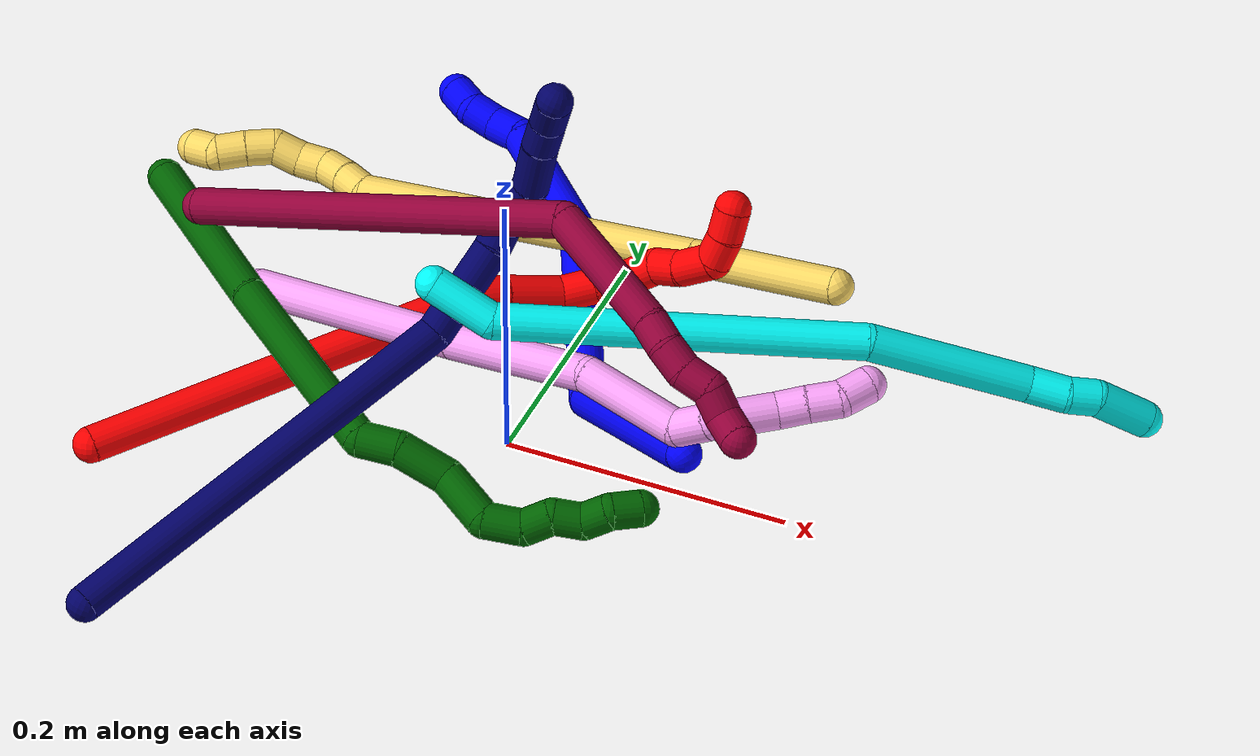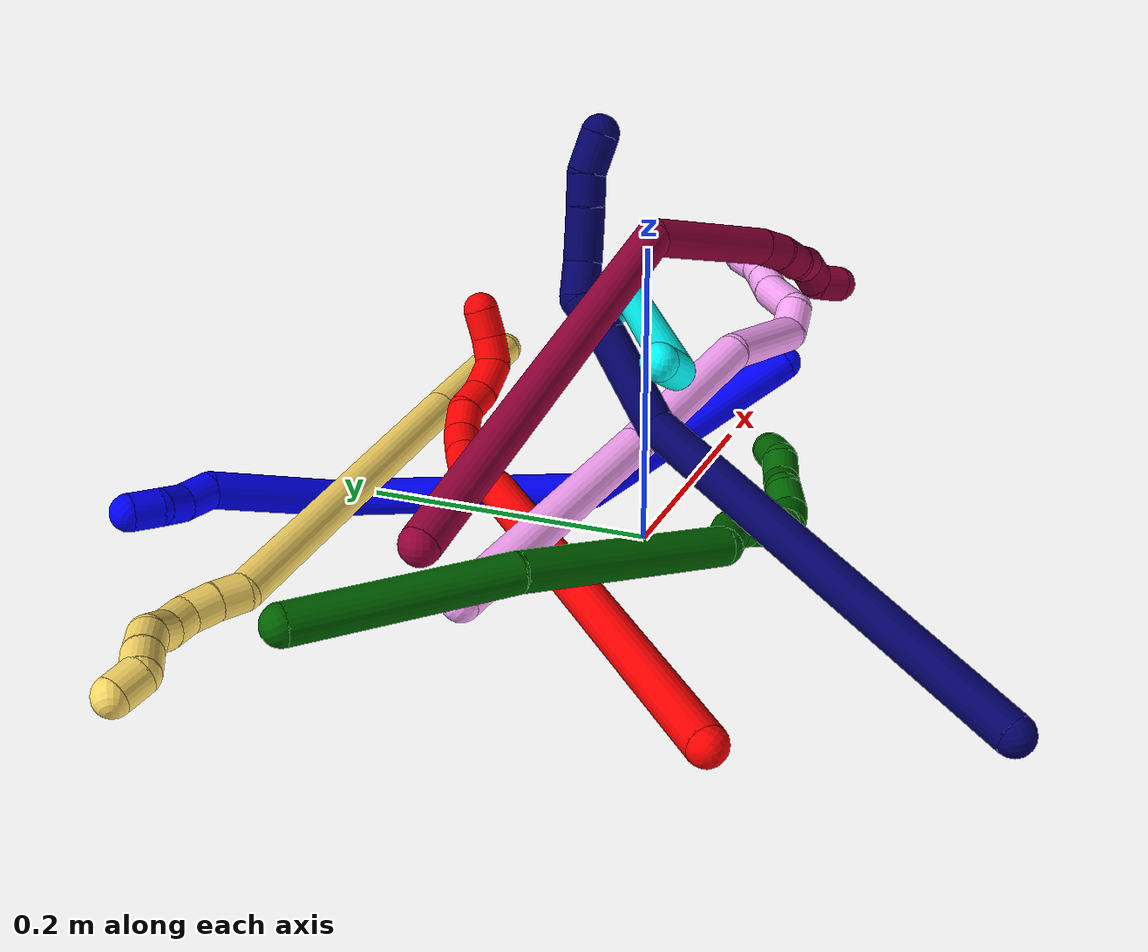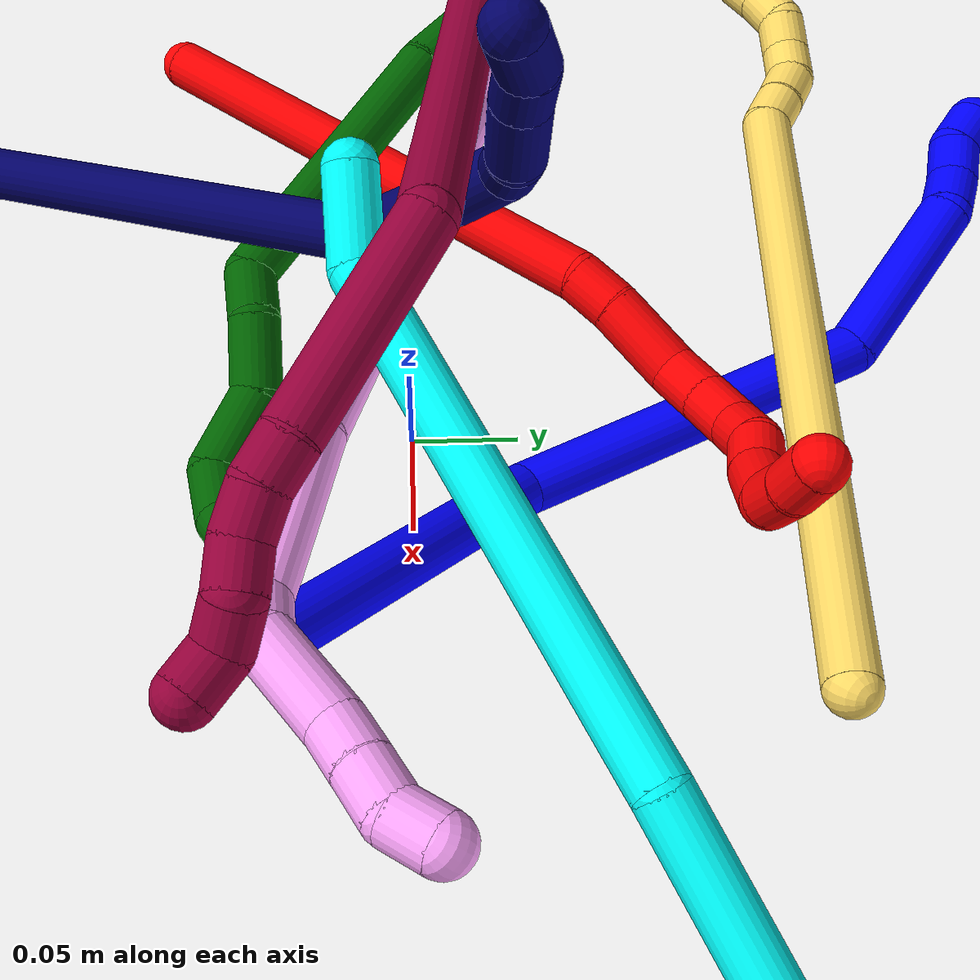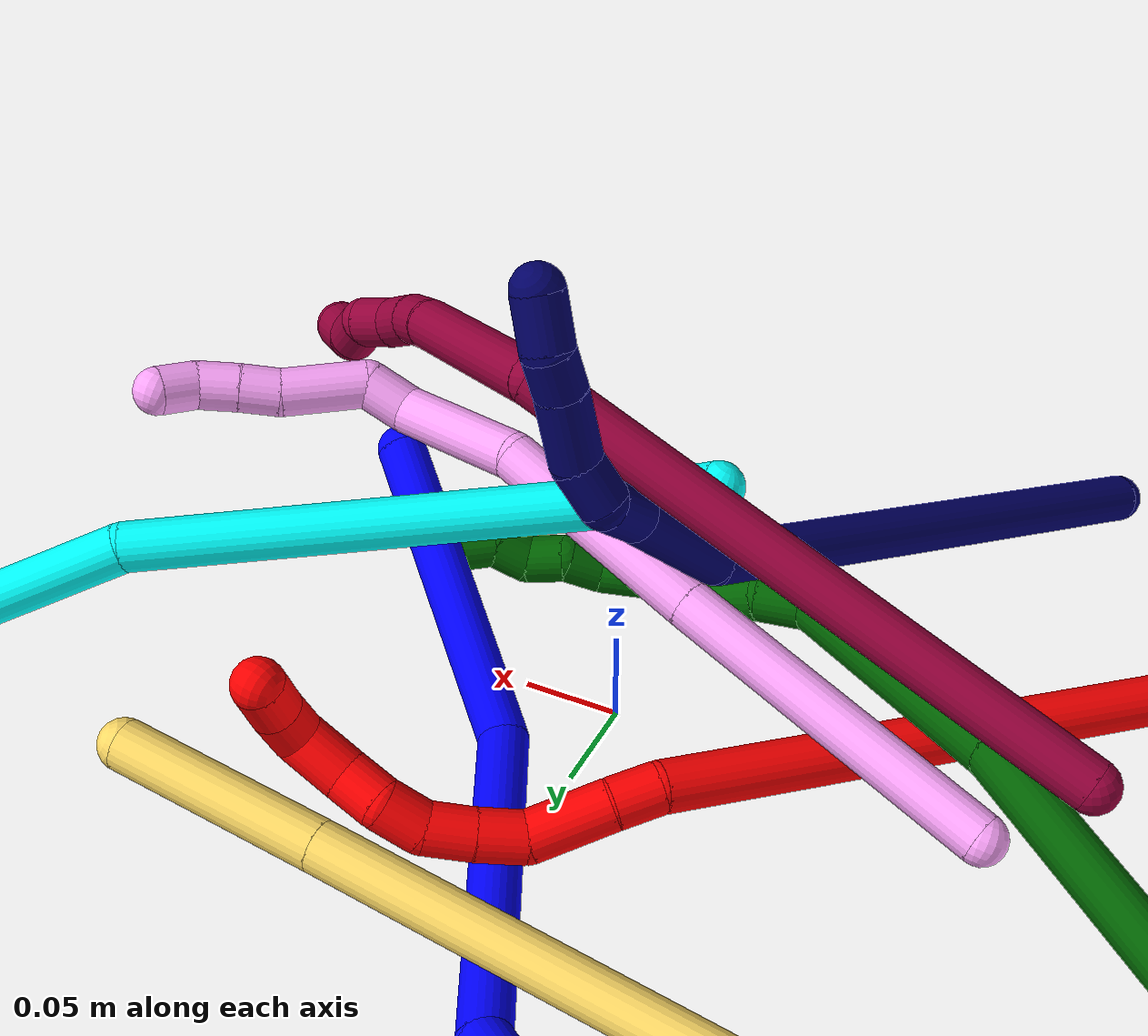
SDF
<sdf version="1.7">
 <world name="default">
  <plugin name="TubeGeneratorPlugin" filename="libtube_generator_plugin.so"/>
  <model name="photoneo_s_sensor">
   <static>1</static>
   <pose>0 0 2 1.57079 1.57079 3.14159</pose>
   <link name="link">
    <inertial><mass>0.1</mass></inertial>
    <sensor name="sensor" type="depth">
     <update_rate>30</update_rate>
     <camera>
      <horizontal_fov>1.22</horizontal_fov>
      <image><width>1920</width><height>1200</height><format>B8G8R8</format></image>
      <clip><near>0.1</near><far>4</far></clip>
      <depth_camera><output>points</output></depth_camera>
     </camera>
     <plugin name="camera_plugin" filename="libgazebo_ros_depth_camera.so">
      <baseline>0.2</baseline>
      <alwaysOn>1</alwaysOn>
      <updateRate>0.0</updateRate>
      <cameraName>camera_ir</cameraName>
      <imageTopicName>/camera/color/image_raw</imageTopicName>
      <cameraInfoTopicName>/camera/color/camera_info</cameraInfoTopicName>
      <depthImageTopicName>/camera/depth/image_raw</depthImageTopicName>
      <depthImageCameraInfoTopicName>/camera/depth/camera_info</depthImageCameraInfoTopicName>
      <pointCloudTopicName>/camera/depth/points</pointCloudTopicName>
      <frameName>fr_optical</frameName>
      <pointCloudCutoff>0.1</pointCloudCutoff>
      <pointCloudCutoffMax>2.0</pointCloudCutoffMax>
      <distortionK1>0</distortionK1>
      <distortionK2>0</distortionK2>
      <distortionK3>0</distortionK3>
      <distortionT1>0</distortionT1>
      <distortionT2>0</distortionT2>
      <CxPrime>0</CxPrime>
      <Cx>0</Cx>
      <Cy>0</Cy>
      <focalLength>0</focalLength>
      <hackBaseline>0</hackBaseline>
     </plugin>
    </sensor>
   </link>
  </model>
  <gravity>0 0 -9.8</gravity>
  <magnetic_field>6e-06 2.3e-05 -4.2e-05</magnetic_field>
  <atmosphere type="adiabatic"/>
  <physics name="default_physics" default="0" type="ode">
   <max_step_size>0.003</max_step_size>
   <real_time_factor>1</real_time_factor>
   <real_time_update_rate>1000</real_time_update_rate>
   <max_contacts>10000</max_contacts>
   <ode>
    <solver>
     <type>quick</type>
     <iters>100</iters>
     <sor>1.3</sor>
     <use_dynamic_moi_rescaling>0</use_dynamic_moi_rescaling>
    </solver>
    <constraints>
     <contact_max_correcting_vel>0</contact_max_correcting_vel>
     <contact_surface_layer>0.001</contact_surface_layer>
     <cfm>0</cfm>
     <erp>0.2</erp>
    </constraints>
   </ode>
  </physics>
  <scene><ambient>0.4 0.4 0.4 1</ambient><background>0.7 0.7 0.7 1</background><shadows>0</shadows></scene>
  <audio><device>default</device></audio>
  <spherical_coordinates>
   <surface_model>EARTH_WGS84</surface_model>
   <latitude_deg>0</latitude_deg>
   <longitude_deg>0</longitude_deg>
   <elevation>0</elevation>
   <heading_deg>0</heading_deg>
  </spherical_coordinates>
  <model name="bin">
   <static>1</static>
   <link name="bottom">
    <collision name="collision-bottom">
     <pose>0 0 -0.01 0 -0 0</pose>
     <geometry><box><size>0.8 0.6 0.02</size></box></geometry>
     <surface>
      <friction><ode><mu>100</mu><mu2>100</mu2></ode></friction>
      <contact><collide_bitmask>65535</collide_bitmask></contact>
     </surface>
    </collision>
   </link>
   <link name="west_wall">
    <collision name="collision-west_wall">
     <pose>-0.41 0 0.1 0 -0 0</pose>
     <geometry><box><size>0.02 0.6 0.2</size></box></geometry>
     <surface>
      <friction><ode><mu>100</mu><mu2>100</mu2></ode></friction>
      <contact><collide_bitmask>65535</collide_bitmask></contact>
     </surface>
    </collision>
   </link>
   <link name="east_wall">
    <collision name="collision-east_wall">
     <pose>0.41 0 0.1 0 -0 0</pose>
     <geometry><box><size>0.02 0.6 0.2</size></box></geometry>
     <surface>
      <friction><ode><mu>100</mu><mu2>100</mu2></ode></friction>
      <contact><collide_bitmask>65535</collide_bitmask></contact>
     </surface>
    </collision>
   </link>
   <link name="south_wall">
    <collision name="collision-south_wall">
     <pose>0 -0.31 0.1 0 -0 0</pose>
     <geometry><box><size>0.8 0.02 0.2</size></box></geometry>
     <surface>
      <friction><ode><mu>100</mu><mu2>100</mu2></ode></friction>
      <contact><collide_bitmask>65535</collide_bitmask></contact>
     </surface>
    </collision>
   </link>
   <link name="north_wall">
    <collision name="collision-north_wall">
     <pose>0 0.31 0.1 0 -0 0</pose>
     <geometry><box><size>0.8 0.02 0.2</size></box></geometry>
     <surface>
      <friction><ode><mu>100</mu><mu2>100</mu2></ode></friction>
      <contact><collide_bitmask>65535</collide_bitmask></contact>
     </surface>
    </collision>
   </link>
  </model>
  <model name="1">
   <static>0</static>
   <link name="1">
    <collision name="collision-cylinder-e_1_1_4">
     <pose>-0.01667 0.081666 0.012676 -1.41681 -0.199033 0.170673</pose>
     <geometry><cylinder><radius>0.0125</radius><length>0.168617</length></cylinder></geometry>
     <surface>
      <friction><ode><mu>1.16</mu><mu2>1.16</mu2><slip1>0</slip1><slip2>0</slip2></ode></friction>
      <contact><ode><kp>1e+06</kp><kd>1</kd><max_vel>0</max_vel><min_depth>0.001</min_depth></ode></contact>
     </surface>
    </collision>
    <visual name="visual-cylinder-e_1_1_4">
     <pose>-0.01667 0.081666 0.012676 -1.41681 -0.199033 0.170673</pose>
     <geometry><cylinder><radius>0.0125</radius><length>0.168617</length></cylinder></geometry>
     <material><ambient>0 0 1 1</ambient></material>
    </visual>
    <collision name="collision-cylinder-e_2_4_5">
     <pose>-0.069349 0.225975 0.079307 -0.859769 -0.410774 0.190448</pose>
     <geometry><cylinder><radius>0.0125</radius><length>0.180354</length></cylinder></geometry>
     <surface>
      <friction><ode><mu>1.16</mu><mu2>1.16</mu2><slip1>0</slip1><slip2>0</slip2></ode></friction>
      <contact><ode><kp>1e+06</kp><kd>1</kd><max_vel>0</max_vel><min_depth>0.001</min_depth></ode></contact>
     </surface>
    </collision>
    <visual name="visual-cylinder-e_2_4_5">
     <pose>-0.069349 0.225975 0.079307 -0.859769 -0.410774 0.190448</pose>
     <geometry><cylinder><radius>0.0125</radius><length>0.180354</length></cylinder></geometry>
     <material><ambient>0 0 1 1</ambient></material>
    </visual>
    <collision name="collision-cylinder-e_3_5_6">
     <pose>-0.139114 0.314005 0.14421 -1.16363 -0.884554 0.603938</pose>
     <geometry><cylinder><radius>0.0125</radius><length>0.087267</length></cylinder></geometry>
     <surface>
      <friction><ode><mu>1.16</mu><mu2>1.16</mu2><slip1>0</slip1><slip2>0</slip2></ode></friction>
      <contact><ode><kp>1e+06</kp><kd>1</kd><max_vel>0</max_vel><min_depth>0.001</min_depth></ode></contact>
     </surface>
    </collision>
    <visual name="visual-cylinder-e_3_5_6">
     <pose>-0.139114 0.314005 0.14421 -1.16363 -0.884554 0.603938</pose>
     <geometry><cylinder><radius>0.0125</radius><length>0.087267</length></cylinder></geometry>
     <material><ambient>0 0 1 1</ambient></material>
    </visual>
    <collision name="collision-cylinder-e_4_6_7">
     <pose>-0.179678 0.348511 0.153518 -1.7489 -0.633638 0.747441</pose>
     <geometry><cylinder><radius>0.0125</radius><length>0.022995</length></cylinder></geometry>
     <surface>
      <friction><ode><mu>1.16</mu><mu2>1.16</mu2><slip1>0</slip1><slip2>0</slip2></ode></friction>
      <contact><ode><kp>1e+06</kp><kd>1</kd><max_vel>0</max_vel><min_depth>0.001</min_depth></ode></contact>
     </surface>
    </collision>
    <visual name="visual-cylinder-e_4_6_7">
     <pose>-0.179678 0.348511 0.153518 -1.7489 -0.633638 0.747441</pose>
     <geometry><cylinder><radius>0.0125</radius><length>0.022995</length></cylinder></geometry>
     <material><ambient>0 0 1 1</ambient></material>
    </visual>
    <collision name="collision-cylinder-e_5_7_8">
     <pose>-0.194711 0.363175 0.14968 -1.94796 -0.943459 1.28802</pose>
     <geometry><cylinder><radius>0.0125</radius><length>0.02032</length></cylinder></geometry>
     <surface>
      <friction><ode><mu>1.16</mu><mu2>1.16</mu2><slip1>0</slip1><slip2>0</slip2></ode></friction>
      <contact><ode><kp>1e+06</kp><kd>1</kd><max_vel>0</max_vel><min_depth>0.001</min_depth></ode></contact>
     </surface>
    </collision>
    <visual name="visual-cylinder-e_5_7_8">
     <pose>-0.194711 0.363175 0.14968 -1.94796 -0.943459 1.28802</pose>
     <geometry><cylinder><radius>0.0125</radius><length>0.02032</length></cylinder></geometry>
     <material><ambient>0 0 1 1</ambient></material>
    </visual>
    <collision name="collision-cylinder-e_6_8_2">
     <pose>-0.209609 0.376286 0.149136 -1.35579 -0.711162 0.581111</pose>
     <geometry><cylinder><radius>0.0125</radius><length>0.020448</length></cylinder></geometry>
     <surface>
      <friction><ode><mu>1.16</mu><mu2>1.16</mu2><slip1>0</slip1><slip2>0</slip2></ode></friction>
      <contact><ode><kp>1e+06</kp><kd>1</kd><max_vel>0</max_vel><min_depth>0.001</min_depth></ode></contact>
     </surface>
    </collision>
    <visual name="visual-cylinder-e_6_8_2">
     <pose>-0.209609 0.376286 0.149136 -1.35579 -0.711162 0.581111</pose>
     <geometry><cylinder><radius>0.0125</radius><length>0.020448</length></cylinder></geometry>
     <material><ambient>0 0 1 1</ambient></material>
    </visual>
    <collision name="collision-sphere-2">
     <pose>-0.216282 0.383854 0.150789 0 -0 0</pose>
     <geometry><sphere><radius>0.0125</radius></sphere></geometry>
     <surface>
      <friction><ode><mu>1.16</mu><mu2>1.16</mu2><slip1>0</slip1><slip2>0</slip2></ode></friction>
      <contact><ode><kp>1e+06</kp><kd>1</kd><max_vel>0</max_vel><min_depth>0.001</min_depth></ode></contact>
     </surface>
    </collision>
    <visual name="visual-sphere-2">
     <pose>-0.216282 0.383854 0.150789 0 -0 0</pose>
     <geometry><sphere><radius>0.0125</radius></sphere></geometry>
     <material><ambient>0 0 1 1</ambient></material>
    </visual>
    <collision name="collision-sphere-4">
     <pose>-0.033339 0.163332 0.025352 0 -0 0</pose>
     <geometry><sphere><radius>0.0125</radius></sphere></geometry>
     <surface>
      <friction><ode><mu>1.16</mu><mu2>1.16</mu2><slip1>0</slip1><slip2>0</slip2></ode></friction>
      <contact><ode><kp>1e+06</kp><kd>1</kd><max_vel>0</max_vel><min_depth>0.001</min_depth></ode></contact>
     </surface>
    </collision>
    <visual name="visual-sphere-4">
     <pose>-0.033339 0.163332 0.025352 0 -0 0</pose>
     <geometry><sphere><radius>0.0125</radius></sphere></geometry>
     <material><ambient>0 0 1 1</ambient></material>
    </visual>
    <collision name="collision-sphere-1">
     <geometry><sphere><radius>0.0125</radius></sphere></geometry>
     <surface>
      <friction><ode><mu>1.16</mu><mu2>1.16</mu2><slip1>0</slip1><slip2>0</slip2></ode></friction>
      <contact><ode><kp>1e+06</kp><kd>1</kd><max_vel>0</max_vel><min_depth>0.001</min_depth></ode></contact>
     </surface>
    </collision>
    <visual name="visual-sphere-1">
     <geometry><sphere><radius>0.0125</radius></sphere></geometry>
     <material><ambient>0 0 1 1</ambient></material>
    </visual>
    <collision name="collision-sphere-8">
     <pose>-0.202936 0.368719 0.147483 0 -0 0</pose>
     <geometry><sphere><radius>0.0125</radius></sphere></geometry>
     <surface>
      <friction><ode><mu>1.16</mu><mu2>1.16</mu2><slip1>0</slip1><slip2>0</slip2></ode></friction>
      <contact><ode><kp>1e+06</kp><kd>1</kd><max_vel>0</max_vel><min_depth>0.001</min_depth></ode></contact>
     </surface>
    </collision>
    <visual name="visual-sphere-8">
     <pose>-0.202936 0.368719 0.147483 0 -0 0</pose>
     <geometry><sphere><radius>0.0125</radius></sphere></geometry>
     <material><ambient>0 0 1 1</ambient></material>
    </visual>
    <collision name="collision-sphere-5">
     <pose>-0.105358 0.288617 0.133262 0 -0 0</pose>
     <geometry><sphere><radius>0.0125</radius></sphere></geometry>
     <surface>
      <friction><ode><mu>1.16</mu><mu2>1.16</mu2><slip1>0</slip1><slip2>0</slip2></ode></friction>
      <contact><ode><kp>1e+06</kp><kd>1</kd><max_vel>0</max_vel><min_depth>0.001</min_depth></ode></contact>
     </surface>
    </collision>
    <visual name="visual-sphere-5">
     <pose>-0.105358 0.288617 0.133262 0 -0 0</pose>
     <geometry><sphere><radius>0.0125</radius></sphere></geometry>
     <material><ambient>0 0 1 1</ambient></material>
    </visual>
    <collision name="collision-sphere-6">
     <pose>-0.17287 0.339392 0.155159 0 -0 0</pose>
     <geometry><sphere><radius>0.0125</radius></sphere></geometry>
     <surface>
      <friction><ode><mu>1.16</mu><mu2>1.16</mu2><slip1>0</slip1><slip2>0</slip2></ode></friction>
      <contact><ode><kp>1e+06</kp><kd>1</kd><max_vel>0</max_vel><min_depth>0.001</min_depth></ode></contact>
     </surface>
    </collision>
    <visual name="visual-sphere-6">
     <pose>-0.17287 0.339392 0.155159 0 -0 0</pose>
     <geometry><sphere><radius>0.0125</radius></sphere></geometry>
     <material><ambient>0 0 1 1</ambient></material>
    </visual>
    <collision name="collision-sphere-7">
     <pose>-0.186485 0.35763 0.151876 0 -0 0</pose>
     <geometry><sphere><radius>0.0125</radius></sphere></geometry>
     <surface>
      <friction><ode><mu>1.16</mu><mu2>1.16</mu2><slip1>0</slip1><slip2>0</slip2></ode></friction>
      <contact><ode><kp>1e+06</kp><kd>1</kd><max_vel>0</max_vel><min_depth>0.001</min_depth></ode></contact>
     </surface>
    </collision>
    <visual name="visual-sphere-7">
     <pose>-0.186485 0.35763 0.151876 0 -0 0</pose>
     <geometry><sphere><radius>0.0125</radius></sphere></geometry>
     <material><ambient>0 0 1 1</ambient></material>
    </visual>
    <inertial>
     <pose>-0.079664 0.210031 0.077293 0 -0 0</pose>
     <mass>0.5</mass>
     <inertia>
      <ixx>0.001032</ixx>
      <ixy>0</ixy>
      <ixz>0</ixz>
      <iyy>0.000674</iyy>
      <iyz>0</iyz>
      <izz>-0.000437</izz>
     </inertia>
    </inertial>
   </link>
   <pose>0.149135 -0.051811 0.082267 -1.23231 0.852265 -0.203313</pose>
  </model>
  <model name="2">
   <static>0</static>
   <link name="2">
    <collision name="collision-cylinder-e_1_1_4">
     <pose>0.071573 0.083416 -0.084898 -2.365 0.541415 -1.1922</pose>
     <geometry><cylinder><radius>0.0125</radius><length>0.277767</length></cylinder></geometry>
     <surface>
      <friction><ode><mu>1.16</mu><mu2>1.16</mu2><slip1>0</slip1><slip2>0</slip2></ode></friction>
      <contact><ode><kp>1e+06</kp><kd>1</kd><max_vel>0</max_vel><min_depth>0.001</min_depth></ode></contact>
     </surface>
    </collision>
    <visual name="visual-cylinder-e_1_1_4">
     <pose>0.071573 0.083416 -0.084898 -2.365 0.541415 -1.1922</pose>
     <geometry><cylinder><radius>0.0125</radius><length>0.277767</length></cylinder></geometry>
     <material><ambient>1 0 0 1</ambient></material>
    </visual>
    <collision name="collision-cylinder-e_2_4_5">
     <pose>0.146439 0.175513 -0.17666 -2.23977 0.289108 -0.584113</pose>
     <geometry><cylinder><radius>0.0125</radius><length>0.023093</length></cylinder></geometry>
     <surface>
      <friction><ode><mu>1.16</mu><mu2>1.16</mu2><slip1>0</slip1><slip2>0</slip2></ode></friction>
      <contact><ode><kp>1e+06</kp><kd>1</kd><max_vel>0</max_vel><min_depth>0.001</min_depth></ode></contact>
     </surface>
    </collision>
    <visual name="visual-cylinder-e_2_4_5">
     <pose>0.146439 0.175513 -0.17666 -2.23977 0.289108 -0.584113</pose>
     <geometry><cylinder><radius>0.0125</radius><length>0.023093</length></cylinder></geometry>
     <material><ambient>1 0 0 1</ambient></material>
    </visual>
    <collision name="collision-cylinder-e_3_5_6">
     <pose>0.152889 0.200053 -0.195952 -2.23552 0.155488 -0.317359</pose>
     <geometry><cylinder><radius>0.0125</radius><length>0.040787</length></cylinder></geometry>
     <surface>
      <friction><ode><mu>1.16</mu><mu2>1.16</mu2><slip1>0</slip1><slip2>0</slip2></ode></friction>
      <contact><ode><kp>1e+06</kp><kd>1</kd><max_vel>0</max_vel><min_depth>0.001</min_depth></ode></contact>
     </surface>
    </collision>
    <visual name="visual-cylinder-e_3_5_6">
     <pose>0.152889 0.200053 -0.195952 -2.23552 0.155488 -0.317359</pose>
     <geometry><cylinder><radius>0.0125</radius><length>0.040787</length></cylinder></geometry>
     <material><ambient>1 0 0 1</ambient></material>
    </visual>
    <collision name="collision-cylinder-e_4_6_7">
     <pose>0.161036 0.221166 -0.218004 -2.64181 0.426927 -1.4082</pose>
     <geometry><cylinder><radius>0.0125</radius><length>0.024095</length></cylinder></geometry>
     <surface>
      <friction><ode><mu>1.16</mu><mu2>1.16</mu2><slip1>0</slip1><slip2>0</slip2></ode></friction>
      <contact><ode><kp>1e+06</kp><kd>1</kd><max_vel>0</max_vel><min_depth>0.001</min_depth></ode></contact>
     </surface>
    </collision>
    <visual name="visual-cylinder-e_4_6_7">
     <pose>0.161036 0.221166 -0.218004 -2.64181 0.426927 -1.4082</pose>
     <geometry><cylinder><radius>0.0125</radius><length>0.024095</length></cylinder></geometry>
     <material><ambient>1 0 0 1</ambient></material>
    </visual>
    <collision name="collision-cylinder-e_5_7_8">
     <pose>0.171047 0.230731 -0.237363 -2.7248 0.440883 -1.62871</pose>
     <geometry><cylinder><radius>0.0125</radius><length>0.023543</length></cylinder></geometry>
     <surface>
      <friction><ode><mu>1.16</mu><mu2>1.16</mu2><slip1>0</slip1><slip2>0</slip2></ode></friction>
      <contact><ode><kp>1e+06</kp><kd>1</kd><max_vel>0</max_vel><min_depth>0.001</min_depth></ode></contact>
     </surface>
    </collision>
    <visual name="visual-cylinder-e_5_7_8">
     <pose>0.171047 0.230731 -0.237363 -2.7248 0.440883 -1.62871</pose>
     <geometry><cylinder><radius>0.0125</radius><length>0.023543</length></cylinder></geometry>
     <material><ambient>1 0 0 1</ambient></material>
    </visual>
    <collision name="collision-cylinder-e_6_8_9">
     <pose>0.181599 0.234856 -0.256491 3.12195 0.531854 3.06951</pose>
     <geometry><cylinder><radius>0.0125</radius><length>0.021803</length></cylinder></geometry>
     <surface>
      <friction><ode><mu>1.16</mu><mu2>1.16</mu2><slip1>0</slip1><slip2>0</slip2></ode></friction>
      <contact><ode><kp>1e+06</kp><kd>1</kd><max_vel>0</max_vel><min_depth>0.001</min_depth></ode></contact>
     </surface>
    </collision>
    <visual name="visual-cylinder-e_6_8_9">
     <pose>0.181599 0.234856 -0.256491 3.12195 0.531854 3.06951</pose>
     <geometry><cylinder><radius>0.0125</radius><length>0.021803</length></cylinder></geometry>
     <material><ambient>1 0 0 1</ambient></material>
    </visual>
    <collision name="collision-cylinder-e_7_9_10">
     <pose>0.18807 0.233338 -0.276072 3.0114 0.091421 1.22376</pose>
     <geometry><cylinder><radius>0.0125</radius><length>0.020634</length></cylinder></geometry>
     <surface>
      <friction><ode><mu>1.16</mu><mu2>1.16</mu2><slip1>0</slip1><slip2>0</slip2></ode></friction>
      <contact><ode><kp>1e+06</kp><kd>1</kd><max_vel>0</max_vel><min_depth>0.001</min_depth></ode></contact>
     </surface>
    </collision>
    <visual name="visual-cylinder-e_7_9_10">
     <pose>0.18807 0.233338 -0.276072 3.0114 0.091421 1.22376</pose>
     <geometry><cylinder><radius>0.0125</radius><length>0.020634</length></cylinder></geometry>
     <material><ambient>1 0 0 1</ambient></material>
    </visual>
    <collision name="collision-cylinder-e_8_10_11">
     <pose>0.193708 0.229751 -0.298847 2.96448 0.351933 2.21532</pose>
     <geometry><cylinder><radius>0.0125</radius><length>0.027246</length></cylinder></geometry>
     <surface>
      <friction><ode><mu>1.16</mu><mu2>1.16</mu2><slip1>0</slip1><slip2>0</slip2></ode></friction>
      <contact><ode><kp>1e+06</kp><kd>1</kd><max_vel>0</max_vel><min_depth>0.001</min_depth></ode></contact>
     </surface>
    </collision>
    <visual name="visual-cylinder-e_8_10_11">
     <pose>0.193708 0.229751 -0.298847 2.96448 0.351933 2.21532</pose>
     <geometry><cylinder><radius>0.0125</radius><length>0.027246</length></cylinder></geometry>
     <material><ambient>1 0 0 1</ambient></material>
    </visual>
    <collision name="collision-cylinder-e_9_11_12">
     <pose>0.207216 0.224751 -0.315456 2.54233 1.06592 2.17673</pose>
     <geometry><cylinder><radius>0.0125</radius><length>0.020137</length></cylinder></geometry>
     <surface>
      <friction><ode><mu>1.16</mu><mu2>1.16</mu2><slip1>0</slip1><slip2>0</slip2></ode></friction>
      <contact><ode><kp>1e+06</kp><kd>1</kd><max_vel>0</max_vel><min_depth>0.001</min_depth></ode></contact>
     </surface>
    </collision>
    <visual name="visual-cylinder-e_9_11_12">
     <pose>0.207216 0.224751 -0.315456 2.54233 1.06592 2.17673</pose>
     <geometry><cylinder><radius>0.0125</radius><length>0.020137</length></cylinder></geometry>
     <material><ambient>1 0 0 1</ambient></material>
    </visual>
    <collision name="collision-cylinder-e_10_12_2">
     <pose>0.225705 0.218908 -0.321914 2.23761 1.18414 1.89106</pose>
     <geometry><cylinder><radius>0.0125</radius><length>0.020896</length></cylinder></geometry>
     <surface>
      <friction><ode><mu>1.16</mu><mu2>1.16</mu2><slip1>0</slip1><slip2>0</slip2></ode></friction>
      <contact><ode><kp>1e+06</kp><kd>1</kd><max_vel>0</max_vel><min_depth>0.001</min_depth></ode></contact>
     </surface>
    </collision>
    <visual name="visual-cylinder-e_10_12_2">
     <pose>0.225705 0.218908 -0.321914 2.23761 1.18414 1.89106</pose>
     <geometry><cylinder><radius>0.0125</radius><length>0.020896</length></cylinder></geometry>
     <material><ambient>1 0 0 1</ambient></material>
    </visual>
    <collision name="collision-sphere-2">
     <pose>0.235381 0.215812 -0.324351 0 -0 0</pose>
     <geometry><sphere><radius>0.0125</radius></sphere></geometry>
     <surface>
      <friction><ode><mu>1.16</mu><mu2>1.16</mu2><slip1>0</slip1><slip2>0</slip2></ode></friction>
      <contact><ode><kp>1e+06</kp><kd>1</kd><max_vel>0</max_vel><min_depth>0.001</min_depth></ode></contact>
     </surface>
    </collision>
    <visual name="visual-sphere-2">
     <pose>0.235381 0.215812 -0.324351 0 -0 0</pose>
     <geometry><sphere><radius>0.0125</radius></sphere></geometry>
     <material><ambient>1 0 0 1</ambient></material>
    </visual>
    <collision name="collision-sphere-12">
     <pose>0.216028 0.222004 -0.319478 0 -0 0</pose>
     <geometry><sphere><radius>0.0125</radius></sphere></geometry>
     <surface>
      <friction><ode><mu>1.16</mu><mu2>1.16</mu2><slip1>0</slip1><slip2>0</slip2></ode></friction>
      <contact><ode><kp>1e+06</kp><kd>1</kd><max_vel>0</max_vel><min_depth>0.001</min_depth></ode></contact>
     </surface>
    </collision>
    <visual name="visual-sphere-12">
     <pose>0.216028 0.222004 -0.319478 0 -0 0</pose>
     <geometry><sphere><radius>0.0125</radius></sphere></geometry>
     <material><ambient>1 0 0 1</ambient></material>
    </visual>
    <collision name="collision-sphere-11">
     <pose>0.198404 0.227498 -0.311435 0 -0 0</pose>
     <geometry><sphere><radius>0.0125</radius></sphere></geometry>
     <surface>
      <friction><ode><mu>1.16</mu><mu2>1.16</mu2><slip1>0</slip1><slip2>0</slip2></ode></friction>
      <contact><ode><kp>1e+06</kp><kd>1</kd><max_vel>0</max_vel><min_depth>0.001</min_depth></ode></contact>
     </surface>
    </collision>
    <visual name="visual-sphere-11">
     <pose>0.198404 0.227498 -0.311435 0 -0 0</pose>
     <geometry><sphere><radius>0.0125</radius></sphere></geometry>
     <material><ambient>1 0 0 1</ambient></material>
    </visual>
    <collision name="collision-sphere-10">
     <pose>0.189011 0.232004 -0.286259 0 -0 0</pose>
     <geometry><sphere><radius>0.0125</radius></sphere></geometry>
     <surface>
      <friction><ode><mu>1.16</mu><mu2>1.16</mu2><slip1>0</slip1><slip2>0</slip2></ode></friction>
      <contact><ode><kp>1e+06</kp><kd>1</kd><max_vel>0</max_vel><min_depth>0.001</min_depth></ode></contact>
     </surface>
    </collision>
    <visual name="visual-sphere-10">
     <pose>0.189011 0.232004 -0.286259 0 -0 0</pose>
     <geometry><sphere><radius>0.0125</radius></sphere></geometry>
     <material><ambient>1 0 0 1</ambient></material>
    </visual>
    <collision name="collision-sphere-9">
     <pose>0.187128 0.234671 -0.265885 0 -0 0</pose>
     <geometry><sphere><radius>0.0125</radius></sphere></geometry>
     <surface>
      <friction><ode><mu>1.16</mu><mu2>1.16</mu2><slip1>0</slip1><slip2>0</slip2></ode></friction>
      <contact><ode><kp>1e+06</kp><kd>1</kd><max_vel>0</max_vel><min_depth>0.001</min_depth></ode></contact>
     </surface>
    </collision>
    <visual name="visual-sphere-9">
     <pose>0.187128 0.234671 -0.265885 0 -0 0</pose>
     <geometry><sphere><radius>0.0125</radius></sphere></geometry>
     <material><ambient>1 0 0 1</ambient></material>
    </visual>
    <collision name="collision-sphere-4">
     <pose>0.143147 0.166831 -0.169796 0 -0 0</pose>
     <geometry><sphere><radius>0.0125</radius></sphere></geometry>
     <surface>
      <friction><ode><mu>1.16</mu><mu2>1.16</mu2><slip1>0</slip1><slip2>0</slip2></ode></friction>
      <contact><ode><kp>1e+06</kp><kd>1</kd><max_vel>0</max_vel><min_depth>0.001</min_depth></ode></contact>
     </surface>
    </collision>
    <visual name="visual-sphere-4">
     <pose>0.143147 0.166831 -0.169796 0 -0 0</pose>
     <geometry><sphere><radius>0.0125</radius></sphere></geometry>
     <material><ambient>1 0 0 1</ambient></material>
    </visual>
    <collision name="collision-sphere-1">
     <geometry><sphere><radius>0.0125</radius></sphere></geometry>
     <surface>
      <friction><ode><mu>1.16</mu><mu2>1.16</mu2><slip1>0</slip1><slip2>0</slip2></ode></friction>
      <contact><ode><kp>1e+06</kp><kd>1</kd><max_vel>0</max_vel><min_depth>0.001</min_depth></ode></contact>
     </surface>
    </collision>
    <visual name="visual-sphere-1">
     <geometry><sphere><radius>0.0125</radius></sphere></geometry>
     <material><ambient>1 0 0 1</ambient></material>
    </visual>
    <collision name="collision-sphere-8">
     <pose>0.176071 0.235041 -0.247097 0 -0 0</pose>
     <geometry><sphere><radius>0.0125</radius></sphere></geometry>
     <surface>
      <friction><ode><mu>1.16</mu><mu2>1.16</mu2><slip1>0</slip1><slip2>0</slip2></ode></friction>
      <contact><ode><kp>1e+06</kp><kd>1</kd><max_vel>0</max_vel><min_depth>0.001</min_depth></ode></contact>
     </surface>
    </collision>
    <visual name="visual-sphere-8">
     <pose>0.176071 0.235041 -0.247097 0 -0 0</pose>
     <geometry><sphere><radius>0.0125</radius></sphere></geometry>
     <material><ambient>1 0 0 1</ambient></material>
    </visual>
    <collision name="collision-sphere-5">
     <pose>0.149731 0.184195 -0.183524 0 -0 0</pose>
     <geometry><sphere><radius>0.0125</radius></sphere></geometry>
     <surface>
      <friction><ode><mu>1.16</mu><mu2>1.16</mu2><slip1>0</slip1><slip2>0</slip2></ode></friction>
      <contact><ode><kp>1e+06</kp><kd>1</kd><max_vel>0</max_vel><min_depth>0.001</min_depth></ode></contact>
     </surface>
    </collision>
    <visual name="visual-sphere-5">
     <pose>0.149731 0.184195 -0.183524 0 -0 0</pose>
     <geometry><sphere><radius>0.0125</radius></sphere></geometry>
     <material><ambient>1 0 0 1</ambient></material>
    </visual>
    <collision name="collision-sphere-6">
     <pose>0.156047 0.215911 -0.208379 0 -0 0</pose>
     <geometry><sphere><radius>0.0125</radius></sphere></geometry>
     <surface>
      <friction><ode><mu>1.16</mu><mu2>1.16</mu2><slip1>0</slip1><slip2>0</slip2></ode></friction>
      <contact><ode><kp>1e+06</kp><kd>1</kd><max_vel>0</max_vel><min_depth>0.001</min_depth></ode></contact>
     </surface>
    </collision>
    <visual name="visual-sphere-6">
     <pose>0.156047 0.215911 -0.208379 0 -0 0</pose>
     <geometry><sphere><radius>0.0125</radius></sphere></geometry>
     <material><ambient>1 0 0 1</ambient></material>
    </visual>
    <collision name="collision-sphere-7">
     <pose>0.166024 0.226421 -0.227629 0 -0 0</pose>
     <geometry><sphere><radius>0.0125</radius></sphere></geometry>
     <surface>
      <friction><ode><mu>1.16</mu><mu2>1.16</mu2><slip1>0</slip1><slip2>0</slip2></ode></friction>
      <contact><ode><kp>1e+06</kp><kd>1</kd><max_vel>0</max_vel><min_depth>0.001</min_depth></ode></contact>
     </surface>
    </collision>
    <visual name="visual-sphere-7">
     <pose>0.166024 0.226421 -0.227629 0 -0 0</pose>
     <geometry><sphere><radius>0.0125</radius></sphere></geometry>
     <material><ambient>1 0 0 1</ambient></material>
    </visual>
    <inertial>
     <pose>0.118824 0.142878 -0.15801 0 -0 0</pose>
     <mass>0.5</mass>
     <inertia>
      <ixx>-0.00084</ixx>
      <ixy>0</ixy>
      <ixz>0</ixz>
      <iyy>-0.001285</iyy>
      <iyz>0</iyz>
      <izz>-0.002046</izz>
     </inertia>
    </inertial>
   </link>
   <pose>-0.247758 -0.122092 0.011492 -1.82597 -0.884318 1.66942</pose>
  </model>
  <model name="3">
   <static>0</static>
   <link name="3">
    <collision name="collision-cylinder-e_1_1_4">
     <pose>0.013129 -0.010411 -0.01483 2.52952 0.627028 1.59654</pose>
     <geometry><cylinder><radius>0.0125</radius><length>0.044751</length></cylinder></geometry>
     <surface>
      <friction><ode><mu>1.16</mu><mu2>1.16</mu2><slip1>0</slip1><slip2>0</slip2></ode></friction>
      <contact><ode><kp>1e+06</kp><kd>1</kd><max_vel>0</max_vel><min_depth>0.001</min_depth></ode></contact>
     </surface>
    </collision>
    <visual name="visual-cylinder-e_1_1_4">
     <pose>0.013129 -0.010411 -0.01483 2.52952 0.627028 1.59654</pose>
     <geometry><cylinder><radius>0.0125</radius><length>0.044751</length></cylinder></geometry>
     <material><ambient>0.003922 1 0.996078 1</ambient></material>
    </visual>
    <collision name="collision-cylinder-e_2_4_5">
     <pose>0.13179 -0.026772 -0.095726 3.05177 1.00964 2.97929</pose>
     <geometry><cylinder><radius>0.0125</radius><length>0.249299</length></cylinder></geometry>
     <surface>
      <friction><ode><mu>1.16</mu><mu2>1.16</mu2><slip1>0</slip1><slip2>0</slip2></ode></friction>
      <contact><ode><kp>1e+06</kp><kd>1</kd><max_vel>0</max_vel><min_depth>0.001</min_depth></ode></contact>
     </surface>
    </collision>
    <visual name="visual-cylinder-e_2_4_5">
     <pose>0.13179 -0.026772 -0.095726 3.05177 1.00964 2.97929</pose>
     <geometry><cylinder><radius>0.0125</radius><length>0.249299</length></cylinder></geometry>
     <material><ambient>0.003922 1 0.996078 1</ambient></material>
    </visual>
    <collision name="collision-cylinder-e_3_5_6">
     <pose>0.275433 -0.035772 -0.206206 3.07303 0.707993 2.95653</pose>
     <geometry><cylinder><radius>0.0125</radius><length>0.117202</length></cylinder></geometry>
     <surface>
      <friction><ode><mu>1.16</mu><mu2>1.16</mu2><slip1>0</slip1><slip2>0</slip2></ode></friction>
      <contact><ode><kp>1e+06</kp><kd>1</kd><max_vel>0</max_vel><min_depth>0.001</min_depth></ode></contact>
     </surface>
    </collision>
    <visual name="visual-cylinder-e_3_5_6">
     <pose>0.275433 -0.035772 -0.206206 3.07303 0.707993 2.95653</pose>
     <geometry><cylinder><radius>0.0125</radius><length>0.117202</length></cylinder></geometry>
     <material><ambient>0.003922 1 0.996078 1</ambient></material>
    </visual>
    <collision name="collision-cylinder-e_4_6_7">
     <pose>0.324003 -0.042079 -0.258889 2.76638 0.866522 2.36272</pose>
     <geometry><cylinder><radius>0.0125</radius><length>0.027455</length></cylinder></geometry>
     <surface>
      <friction><ode><mu>1.16</mu><mu2>1.16</mu2><slip1>0</slip1><slip2>0</slip2></ode></friction>
      <contact><ode><kp>1e+06</kp><kd>1</kd><max_vel>0</max_vel><min_depth>0.001</min_depth></ode></contact>
     </surface>
    </collision>
    <visual name="visual-cylinder-e_4_6_7">
     <pose>0.324003 -0.042079 -0.258889 2.76638 0.866522 2.36272</pose>
     <geometry><cylinder><radius>0.0125</radius><length>0.027455</length></cylinder></geometry>
     <material><ambient>0.003922 1 0.996078 1</ambient></material>
    </visual>
    <collision name="collision-cylinder-e_5_7_8">
     <pose>0.342283 -0.045136 -0.273892 -3.11192 0.859579 -3.07687</pose>
     <geometry><cylinder><radius>0.0125</radius><length>0.02064</length></cylinder></geometry>
     <surface>
      <friction><ode><mu>1.16</mu><mu2>1.16</mu2><slip1>0</slip1><slip2>0</slip2></ode></friction>
      <contact><ode><kp>1e+06</kp><kd>1</kd><max_vel>0</max_vel><min_depth>0.001</min_depth></ode></contact>
     </surface>
    </collision>
    <visual name="visual-cylinder-e_5_7_8">
     <pose>0.342283 -0.045136 -0.273892 -3.11192 0.859579 -3.07687</pose>
     <geometry><cylinder><radius>0.0125</radius><length>0.02064</length></cylinder></geometry>
     <material><ambient>0.003922 1 0.996078 1</ambient></material>
    </visual>
    <collision name="collision-cylinder-e_6_8_2">
     <pose>0.359912 -0.045959 -0.298398 3.08413 0.503722 2.91916</pose>
     <geometry><cylinder><radius>0.0125</radius><length>0.040653</length></cylinder></geometry>
     <surface>
      <friction><ode><mu>1.16</mu><mu2>1.16</mu2><slip1>0</slip1><slip2>0</slip2></ode></friction>
      <contact><ode><kp>1e+06</kp><kd>1</kd><max_vel>0</max_vel><min_depth>0.001</min_depth></ode></contact>
     </surface>
    </collision>
    <visual name="visual-cylinder-e_6_8_2">
     <pose>0.359912 -0.045959 -0.298398 3.08413 0.503722 2.91916</pose>
     <geometry><cylinder><radius>0.0125</radius><length>0.040653</length></cylinder></geometry>
     <material><ambient>0.003922 1 0.996078 1</ambient></material>
    </visual>
    <collision name="collision-sphere-2">
     <pose>0.369723 -0.046981 -0.31617 0 -0 0</pose>
     <geometry><sphere><radius>0.0125</radius></sphere></geometry>
     <surface>
      <friction><ode><mu>1.16</mu><mu2>1.16</mu2><slip1>0</slip1><slip2>0</slip2></ode></friction>
      <contact><ode><kp>1e+06</kp><kd>1</kd><max_vel>0</max_vel><min_depth>0.001</min_depth></ode></contact>
     </surface>
    </collision>
    <visual name="visual-sphere-2">
     <pose>0.369723 -0.046981 -0.31617 0 -0 0</pose>
     <geometry><sphere><radius>0.0125</radius></sphere></geometry>
     <material><ambient>0.003922 1 0.996078 1</ambient></material>
    </visual>
    <collision name="collision-sphere-4">
     <pose>0.026257 -0.020821 -0.029659 0 -0 0</pose>
     <geometry><sphere><radius>0.0125</radius></sphere></geometry>
     <surface>
      <friction><ode><mu>1.16</mu><mu2>1.16</mu2><slip1>0</slip1><slip2>0</slip2></ode></friction>
      <contact><ode><kp>1e+06</kp><kd>1</kd><max_vel>0</max_vel><min_depth>0.001</min_depth></ode></contact>
     </surface>
    </collision>
    <visual name="visual-sphere-4">
     <pose>0.026257 -0.020821 -0.029659 0 -0 0</pose>
     <geometry><sphere><radius>0.0125</radius></sphere></geometry>
     <material><ambient>0.003922 1 0.996078 1</ambient></material>
    </visual>
    <collision name="collision-sphere-1">
     <geometry><sphere><radius>0.0125</radius></sphere></geometry>
     <surface>
      <friction><ode><mu>1.16</mu><mu2>1.16</mu2><slip1>0</slip1><slip2>0</slip2></ode></friction>
      <contact><ode><kp>1e+06</kp><kd>1</kd><max_vel>0</max_vel><min_depth>0.001</min_depth></ode></contact>
     </surface>
    </collision>
    <visual name="visual-sphere-1">
     <geometry><sphere><radius>0.0125</radius></sphere></geometry>
     <material><ambient>0.003922 1 0.996078 1</ambient></material>
    </visual>
    <collision name="collision-sphere-8">
     <pose>0.350101 -0.044936 -0.280626 0 -0 0</pose>
     <geometry><sphere><radius>0.0125</radius></sphere></geometry>
     <surface>
      <friction><ode><mu>1.16</mu><mu2>1.16</mu2><slip1>0</slip1><slip2>0</slip2></ode></friction>
      <contact><ode><kp>1e+06</kp><kd>1</kd><max_vel>0</max_vel><min_depth>0.001</min_depth></ode></contact>
     </surface>
    </collision>
    <visual name="visual-sphere-8">
     <pose>0.350101 -0.044936 -0.280626 0 -0 0</pose>
     <geometry><sphere><radius>0.0125</radius></sphere></geometry>
     <material><ambient>0.003922 1 0.996078 1</ambient></material>
    </visual>
    <collision name="collision-sphere-5">
     <pose>0.237324 -0.032722 -0.161793 0 -0 0</pose>
     <geometry><sphere><radius>0.0125</radius></sphere></geometry>
     <surface>
      <friction><ode><mu>1.16</mu><mu2>1.16</mu2><slip1>0</slip1><slip2>0</slip2></ode></friction>
      <contact><ode><kp>1e+06</kp><kd>1</kd><max_vel>0</max_vel><min_depth>0.001</min_depth></ode></contact>
     </surface>
    </collision>
    <visual name="visual-sphere-5">
     <pose>0.237324 -0.032722 -0.161793 0 -0 0</pose>
     <geometry><sphere><radius>0.0125</radius></sphere></geometry>
     <material><ambient>0.003922 1 0.996078 1</ambient></material>
    </visual>
    <collision name="collision-sphere-6">
     <pose>0.313541 -0.038821 -0.250619 0 -0 0</pose>
     <geometry><sphere><radius>0.0125</radius></sphere></geometry>
     <surface>
      <friction><ode><mu>1.16</mu><mu2>1.16</mu2><slip1>0</slip1><slip2>0</slip2></ode></friction>
      <contact><ode><kp>1e+06</kp><kd>1</kd><max_vel>0</max_vel><min_depth>0.001</min_depth></ode></contact>
     </surface>
    </collision>
    <visual name="visual-sphere-6">
     <pose>0.313541 -0.038821 -0.250619 0 -0 0</pose>
     <geometry><sphere><radius>0.0125</radius></sphere></geometry>
     <material><ambient>0.003922 1 0.996078 1</ambient></material>
    </visual>
    <collision name="collision-sphere-7">
     <pose>0.334465 -0.045336 -0.267159 0 -0 0</pose>
     <geometry><sphere><radius>0.0125</radius></sphere></geometry>
     <surface>
      <friction><ode><mu>1.16</mu><mu2>1.16</mu2><slip1>0</slip1><slip2>0</slip2></ode></friction>
      <contact><ode><kp>1e+06</kp><kd>1</kd><max_vel>0</max_vel><min_depth>0.001</min_depth></ode></contact>
     </surface>
    </collision>
    <visual name="visual-sphere-7">
     <pose>0.334465 -0.045336 -0.267159 0 -0 0</pose>
     <geometry><sphere><radius>0.0125</radius></sphere></geometry>
     <material><ambient>0.003922 1 0.996078 1</ambient></material>
    </visual>
    <inertial>
     <pose>0.192631 -0.030576 -0.147175 0 -0 0</pose>
     <mass>0.5</mass>
     <inertia>
      <ixx>-0.000625</ixx>
      <ixy>0</ixy>
      <ixz>0</ixz>
      <iyy>0.001584</iyy>
      <iyz>0</iyz>
      <izz>-0.001154</izz>
     </inertia>
    </inertial>
   </link>
   <pose>-0.041315 -0.022573 0.141109 0.260429 -0.440562 0.368485</pose>
  </model>
  <model name="4">
   <static>0</static>
   <link name="4">
    <collision name="collision-cylinder-e_1_1_4">
     <pose>0.075716 -0.03732 0.022472 1.02881 1.0487 0.631822</pose>
     <geometry><cylinder><radius>0.0125</radius><length>0.174707</length></cylinder></geometry>
     <surface>
      <friction><ode><mu>1.16</mu><mu2>1.16</mu2><slip1>0</slip1><slip2>0</slip2></ode></friction>
      <contact><ode><kp>1e+06</kp><kd>1</kd><max_vel>0</max_vel><min_depth>0.001</min_depth></ode></contact>
     </surface>
    </collision>
    <visual name="visual-cylinder-e_1_1_4">
     <pose>0.075716 -0.03732 0.022472 1.02881 1.0487 0.631822</pose>
     <geometry><cylinder><radius>0.0125</radius><length>0.174707</length></cylinder></geometry>
     <material><ambient>1 0.65098 0.996078 1</ambient></material>
    </visual>
    <collision name="collision-cylinder-e_2_4_5">
     <pose>0.202685 -0.098476 0.061635 0.959903 1.05442 0.588508</pose>
     <geometry><cylinder><radius>0.0125</radius><length>0.117875</length></cylinder></geometry>
     <surface>
      <friction><ode><mu>1.16</mu><mu2>1.16</mu2><slip1>0</slip1><slip2>0</slip2></ode></friction>
      <contact><ode><kp>1e+06</kp><kd>1</kd><max_vel>0</max_vel><min_depth>0.001</min_depth></ode></contact>
     </surface>
    </collision>
    <visual name="visual-cylinder-e_2_4_5">
     <pose>0.202685 -0.098476 0.061635 0.959903 1.05442 0.588508</pose>
     <geometry><cylinder><radius>0.0125</radius><length>0.117875</length></cylinder></geometry>
     <material><ambient>1 0.65098 0.996078 1</ambient></material>
    </visual>
    <collision name="collision-cylinder-e_3_5_6">
     <pose>0.282914 -0.145894 0.079052 1.54002 0.88746 0.863821</pose>
     <geometry><cylinder><radius>0.0125</radius><length>0.074731</length></cylinder></geometry>
     <surface>
      <friction><ode><mu>1.16</mu><mu2>1.16</mu2><slip1>0</slip1><slip2>0</slip2></ode></friction>
      <contact><ode><kp>1e+06</kp><kd>1</kd><max_vel>0</max_vel><min_depth>0.001</min_depth></ode></contact>
     </surface>
    </collision>
    <visual name="visual-cylinder-e_3_5_6">
     <pose>0.282914 -0.145894 0.079052 1.54002 0.88746 0.863821</pose>
     <geometry><cylinder><radius>0.0125</radius><length>0.074731</length></cylinder></geometry>
     <material><ambient>1 0.65098 0.996078 1</ambient></material>
    </visual>
    <collision name="collision-cylinder-e_4_6_7">
     <pose>0.32421 -0.169884 0.082065 0.17709 1.38444 0.146941</pose>
     <geometry><cylinder><radius>0.0125</radius><length>0.025073</length></cylinder></geometry>
     <surface>
      <friction><ode><mu>1.16</mu><mu2>1.16</mu2><slip1>0</slip1><slip2>0</slip2></ode></friction>
      <contact><ode><kp>1e+06</kp><kd>1</kd><max_vel>0</max_vel><min_depth>0.001</min_depth></ode></contact>
     </surface>
    </collision>
    <visual name="visual-cylinder-e_4_6_7">
     <pose>0.32421 -0.169884 0.082065 0.17709 1.38444 0.146941</pose>
     <geometry><cylinder><radius>0.0125</radius><length>0.025073</length></cylinder></geometry>
     <material><ambient>1 0.65098 0.996078 1</ambient></material>
    </visual>
    <collision name="collision-cylinder-e_5_7_8">
     <pose>0.355931 -0.168081 0.073722 -2.9364 1.06063 -2.79394</pose>
     <geometry><cylinder><radius>0.0125</radius><length>0.044466</length></cylinder></geometry>
     <surface>
      <friction><ode><mu>1.16</mu><mu2>1.16</mu2><slip1>0</slip1><slip2>0</slip2></ode></friction>
      <contact><ode><kp>1e+06</kp><kd>1</kd><max_vel>0</max_vel><min_depth>0.001</min_depth></ode></contact>
     </surface>
    </collision>
    <visual name="visual-cylinder-e_5_7_8">
     <pose>0.355931 -0.168081 0.073722 -2.9364 1.06063 -2.79394</pose>
     <geometry><cylinder><radius>0.0125</radius><length>0.044466</length></cylinder></geometry>
     <material><ambient>1 0.65098 0.996078 1</ambient></material>
    </visual>
    <collision name="collision-cylinder-e_6_8_9">
     <pose>0.385221 -0.16495 0.060249 -2.82937 1.27729 -2.72379</pose>
     <geometry><cylinder><radius>0.0125</radius><length>0.02066</length></cylinder></geometry>
     <surface>
      <friction><ode><mu>1.16</mu><mu2>1.16</mu2><slip1>0</slip1><slip2>0</slip2></ode></friction>
      <contact><ode><kp>1e+06</kp><kd>1</kd><max_vel>0</max_vel><min_depth>0.001</min_depth></ode></contact>
     </surface>
    </collision>
    <visual name="visual-cylinder-e_6_8_9">
     <pose>0.385221 -0.16495 0.060249 -2.82937 1.27729 -2.72379</pose>
     <geometry><cylinder><radius>0.0125</radius><length>0.02066</length></cylinder></geometry>
     <material><ambient>1 0.65098 0.996078 1</ambient></material>
    </visual>
    <collision name="collision-cylinder-e_7_9_10">
     <pose>0.405445 -0.163462 0.053867 -2.98166 1.23705 -2.91733</pose>
     <geometry><cylinder><radius>0.0125</radius><length>0.021879</length></cylinder></geometry>
     <surface>
      <friction><ode><mu>1.16</mu><mu2>1.16</mu2><slip1>0</slip1><slip2>0</slip2></ode></friction>
      <contact><ode><kp>1e+06</kp><kd>1</kd><max_vel>0</max_vel><min_depth>0.001</min_depth></ode></contact>
     </surface>
    </collision>
    <visual name="visual-cylinder-e_7_9_10">
     <pose>0.405445 -0.163462 0.053867 -2.98166 1.23705 -2.91733</pose>
     <geometry><cylinder><radius>0.0125</radius><length>0.021879</length></cylinder></geometry>
     <material><ambient>1 0.65098 0.996078 1</ambient></material>
    </visual>
    <collision name="collision-cylinder-e_8_10_2">
     <pose>0.423677 -0.15863 0.045263 -2.44233 0.873093 -1.81491</pose>
     <geometry><cylinder><radius>0.0125</radius><length>0.020608</length></cylinder></geometry>
     <surface>
      <friction><ode><mu>1.16</mu><mu2>1.16</mu2><slip1>0</slip1><slip2>0</slip2></ode></friction>
      <contact><ode><kp>1e+06</kp><kd>1</kd><max_vel>0</max_vel><min_depth>0.001</min_depth></ode></contact>
     </surface>
    </collision>
    <visual name="visual-cylinder-e_8_10_2">
     <pose>0.423677 -0.15863 0.045263 -2.44233 0.873093 -1.81491</pose>
     <geometry><cylinder><radius>0.0125</radius><length>0.020608</length></cylinder></geometry>
     <material><ambient>1 0.65098 0.996078 1</ambient></material>
    </visual>
    <collision name="collision-sphere-2">
     <pose>0.431573 -0.154369 0.040196 0 -0 0</pose>
     <geometry><sphere><radius>0.0125</radius></sphere></geometry>
     <surface>
      <friction><ode><mu>1.16</mu><mu2>1.16</mu2><slip1>0</slip1><slip2>0</slip2></ode></friction>
      <contact><ode><kp>1e+06</kp><kd>1</kd><max_vel>0</max_vel><min_depth>0.001</min_depth></ode></contact>
     </surface>
    </collision>
    <visual name="visual-sphere-2">
     <pose>0.431573 -0.154369 0.040196 0 -0 0</pose>
     <geometry><sphere><radius>0.0125</radius></sphere></geometry>
     <material><ambient>1 0.65098 0.996078 1</ambient></material>
    </visual>
    <collision name="collision-sphere-10">
     <pose>0.415781 -0.162891 0.050329 0 -0 0</pose>
     <geometry><sphere><radius>0.0125</radius></sphere></geometry>
     <surface>
      <friction><ode><mu>1.16</mu><mu2>1.16</mu2><slip1>0</slip1><slip2>0</slip2></ode></friction>
      <contact><ode><kp>1e+06</kp><kd>1</kd><max_vel>0</max_vel><min_depth>0.001</min_depth></ode></contact>
     </surface>
    </collision>
    <visual name="visual-sphere-10">
     <pose>0.415781 -0.162891 0.050329 0 -0 0</pose>
     <geometry><sphere><radius>0.0125</radius></sphere></geometry>
     <material><ambient>1 0.65098 0.996078 1</ambient></material>
    </visual>
    <collision name="collision-sphere-9">
     <pose>0.395109 -0.164032 0.057405 0 -0 0</pose>
     <geometry><sphere><radius>0.0125</radius></sphere></geometry>
     <surface>
      <friction><ode><mu>1.16</mu><mu2>1.16</mu2><slip1>0</slip1><slip2>0</slip2></ode></friction>
      <contact><ode><kp>1e+06</kp><kd>1</kd><max_vel>0</max_vel><min_depth>0.001</min_depth></ode></contact>
     </surface>
    </collision>
    <visual name="visual-sphere-9">
     <pose>0.395109 -0.164032 0.057405 0 -0 0</pose>
     <geometry><sphere><radius>0.0125</radius></sphere></geometry>
     <material><ambient>1 0.65098 0.996078 1</ambient></material>
    </visual>
    <collision name="collision-sphere-4">
     <pose>0.151432 -0.07464 0.044944 0 -0 0</pose>
     <geometry><sphere><radius>0.0125</radius></sphere></geometry>
     <surface>
      <friction><ode><mu>1.16</mu><mu2>1.16</mu2><slip1>0</slip1><slip2>0</slip2></ode></friction>
      <contact><ode><kp>1e+06</kp><kd>1</kd><max_vel>0</max_vel><min_depth>0.001</min_depth></ode></contact>
     </surface>
    </collision>
    <visual name="visual-sphere-4">
     <pose>0.151432 -0.07464 0.044944 0 -0 0</pose>
     <geometry><sphere><radius>0.0125</radius></sphere></geometry>
     <material><ambient>1 0.65098 0.996078 1</ambient></material>
    </visual>
    <collision name="collision-sphere-1">
     <geometry><sphere><radius>0.0125</radius></sphere></geometry>
     <surface>
      <friction><ode><mu>1.16</mu><mu2>1.16</mu2><slip1>0</slip1><slip2>0</slip2></ode></friction>
      <contact><ode><kp>1e+06</kp><kd>1</kd><max_vel>0</max_vel><min_depth>0.001</min_depth></ode></contact>
     </surface>
    </collision>
    <visual name="visual-sphere-1">
     <geometry><sphere><radius>0.0125</radius></sphere></geometry>
     <material><ambient>1 0.65098 0.996078 1</ambient></material>
    </visual>
    <collision name="collision-sphere-8">
     <pose>0.375333 -0.165868 0.063093 0 -0 0</pose>
     <geometry><sphere><radius>0.0125</radius></sphere></geometry>
     <surface>
      <friction><ode><mu>1.16</mu><mu2>1.16</mu2><slip1>0</slip1><slip2>0</slip2></ode></friction>
      <contact><ode><kp>1e+06</kp><kd>1</kd><max_vel>0</max_vel><min_depth>0.001</min_depth></ode></contact>
     </surface>
    </collision>
    <visual name="visual-sphere-8">
     <pose>0.375333 -0.165868 0.063093 0 -0 0</pose>
     <geometry><sphere><radius>0.0125</radius></sphere></geometry>
     <material><ambient>1 0.65098 0.996078 1</ambient></material>
    </visual>
    <collision name="collision-sphere-5">
     <pose>0.253938 -0.122313 0.078326 0 -0 0</pose>
     <geometry><sphere><radius>0.0125</radius></sphere></geometry>
     <surface>
      <friction><ode><mu>1.16</mu><mu2>1.16</mu2><slip1>0</slip1><slip2>0</slip2></ode></friction>
      <contact><ode><kp>1e+06</kp><kd>1</kd><max_vel>0</max_vel><min_depth>0.001</min_depth></ode></contact>
     </surface>
    </collision>
    <visual name="visual-sphere-5">
     <pose>0.253938 -0.122313 0.078326 0 -0 0</pose>
     <geometry><sphere><radius>0.0125</radius></sphere></geometry>
     <material><ambient>1 0.65098 0.996078 1</ambient></material>
    </visual>
    <collision name="collision-sphere-6">
     <pose>0.31189 -0.169474 0.079778 0 -0 0</pose>
     <geometry><sphere><radius>0.0125</radius></sphere></geometry>
     <surface>
      <friction><ode><mu>1.16</mu><mu2>1.16</mu2><slip1>0</slip1><slip2>0</slip2></ode></friction>
      <contact><ode><kp>1e+06</kp><kd>1</kd><max_vel>0</max_vel><min_depth>0.001</min_depth></ode></contact>
     </surface>
    </collision>
    <visual name="visual-sphere-6">
     <pose>0.31189 -0.169474 0.079778 0 -0 0</pose>
     <geometry><sphere><radius>0.0125</radius></sphere></geometry>
     <material><ambient>1 0.65098 0.996078 1</ambient></material>
    </visual>
    <collision name="collision-sphere-7">
     <pose>0.336529 -0.170293 0.084351 0 -0 0</pose>
     <geometry><sphere><radius>0.0125</radius></sphere></geometry>
     <surface>
      <friction><ode><mu>1.16</mu><mu2>1.16</mu2><slip1>0</slip1><slip2>0</slip2></ode></friction>
      <contact><ode><kp>1e+06</kp><kd>1</kd><max_vel>0</max_vel><min_depth>0.001</min_depth></ode></contact>
     </surface>
    </collision>
    <visual name="visual-sphere-7">
     <pose>0.336529 -0.170293 0.084351 0 -0 0</pose>
     <geometry><sphere><radius>0.0125</radius></sphere></geometry>
     <material><ambient>1 0.65098 0.996078 1</ambient></material>
    </visual>
    <inertial>
     <pose>0.215557 -0.102035 0.051581 0 -0 0</pose>
     <mass>0.5</mass>
     <inertia>
      <ixx>0.000471</ixx>
      <ixy>0</ixy>
      <ixz>0</ixz>
      <iyy>0.000722</iyy>
      <iyz>0</iyz>
      <izz>-0.000282</izz>
     </inertia>
    </inertial>
   </link>
   <pose>-0.199195 0.03995 0.040616 0.679294 -0.34966 0.263675</pose>
  </model>
  <model name="5">
   <static>0</static>
   <link name="5">
    <collision name="collision-cylinder-e_1_1_4">
     <pose>-0.033826 0.000779 0.040991 -0.019004 -0.689836 0.006828</pose>
     <geometry><cylinder><radius>0.0125</radius><length>0.106303</length></cylinder></geometry>
     <surface>
      <friction><ode><mu>1.16</mu><mu2>1.16</mu2><slip1>0</slip1><slip2>0</slip2></ode></friction>
      <contact><ode><kp>1e+06</kp><kd>1</kd><max_vel>0</max_vel><min_depth>0.001</min_depth></ode></contact>
     </surface>
    </collision>
    <visual name="visual-cylinder-e_1_1_4">
     <pose>-0.033826 0.000779 0.040991 -0.019004 -0.689836 0.006828</pose>
     <geometry><cylinder><radius>0.0125</radius><length>0.106303</length></cylinder></geometry>
     <material><ambient>1 0.858824 0.4 1</ambient></material>
    </visual>
    <collision name="collision-cylinder-e_2_4_5">
     <pose>-0.147277 0.001997 0.180029 -0.004477 -0.682073 0.001589</pose>
     <geometry><cylinder><radius>0.0125</radius><length>0.252614</length></cylinder></geometry>
     <surface>
      <friction><ode><mu>1.16</mu><mu2>1.16</mu2><slip1>0</slip1><slip2>0</slip2></ode></friction>
      <contact><ode><kp>1e+06</kp><kd>1</kd><max_vel>0</max_vel><min_depth>0.001</min_depth></ode></contact>
     </surface>
    </collision>
    <visual name="visual-cylinder-e_2_4_5">
     <pose>-0.147277 0.001997 0.180029 -0.004477 -0.682073 0.001589</pose>
     <geometry><cylinder><radius>0.0125</radius><length>0.252614</length></cylinder></geometry>
     <material><ambient>1 0.858824 0.4 1</ambient></material>
    </visual>
    <collision name="collision-cylinder-e_3_5_6">
     <pose>-0.23574 0.000735 0.282569 0.361908 -1.07296 -0.216739</pose>
     <geometry><cylinder><radius>0.0125</radius><length>0.020121</length></cylinder></geometry>
     <surface>
      <friction><ode><mu>1.16</mu><mu2>1.16</mu2><slip1>0</slip1><slip2>0</slip2></ode></friction>
      <contact><ode><kp>1e+06</kp><kd>1</kd><max_vel>0</max_vel><min_depth>0.001</min_depth></ode></contact>
     </surface>
    </collision>
    <visual name="visual-cylinder-e_3_5_6">
     <pose>-0.23574 0.000735 0.282569 0.361908 -1.07296 -0.216739</pose>
     <geometry><cylinder><radius>0.0125</radius><length>0.020121</length></cylinder></geometry>
     <material><ambient>1 0.858824 0.4 1</ambient></material>
    </visual>
    <collision name="collision-cylinder-e_4_6_7">
     <pose>-0.253145 -0.003115 0.292554 0.372988 -0.967788 -0.19769</pose>
     <geometry><cylinder><radius>0.0125</radius><length>0.0208</length></cylinder></geometry>
     <surface>
      <friction><ode><mu>1.16</mu><mu2>1.16</mu2><slip1>0</slip1><slip2>0</slip2></ode></friction>
      <contact><ode><kp>1e+06</kp><kd>1</kd><max_vel>0</max_vel><min_depth>0.001</min_depth></ode></contact>
     </surface>
    </collision>
    <visual name="visual-cylinder-e_4_6_7">
     <pose>-0.253145 -0.003115 0.292554 0.372988 -0.967788 -0.19769</pose>
     <geometry><cylinder><radius>0.0125</radius><length>0.0208</length></cylinder></geometry>
     <material><ambient>1 0.858824 0.4 1</ambient></material>
    </visual>
    <collision name="collision-cylinder-e_5_7_8">
     <pose>-0.268409 -0.003934 0.30546 -0.177613 -0.726857 0.067703</pose>
     <geometry><cylinder><radius>0.0125</radius><length>0.020158</length></cylinder></geometry>
     <surface>
      <friction><ode><mu>1.16</mu><mu2>1.16</mu2><slip1>0</slip1><slip2>0</slip2></ode></friction>
      <contact><ode><kp>1e+06</kp><kd>1</kd><max_vel>0</max_vel><min_depth>0.001</min_depth></ode></contact>
     </surface>
    </collision>
    <visual name="visual-cylinder-e_5_7_8">
     <pose>-0.268409 -0.003934 0.30546 -0.177613 -0.726857 0.067703</pose>
     <geometry><cylinder><radius>0.0125</radius><length>0.020158</length></cylinder></geometry>
     <material><ambient>1 0.858824 0.4 1</ambient></material>
    </visual>
    <collision name="collision-cylinder-e_6_8_9">
     <pose>-0.282014 0.00178 0.318626 -0.651003 -0.762441 0.268931</pose>
     <geometry><cylinder><radius>0.0125</radius><length>0.020001</length></cylinder></geometry>
     <surface>
      <friction><ode><mu>1.16</mu><mu2>1.16</mu2><slip1>0</slip1><slip2>0</slip2></ode></friction>
      <contact><ode><kp>1e+06</kp><kd>1</kd><max_vel>0</max_vel><min_depth>0.001</min_depth></ode></contact>
     </surface>
    </collision>
    <visual name="visual-cylinder-e_6_8_9">
     <pose>-0.282014 0.00178 0.318626 -0.651003 -0.762441 0.268931</pose>
     <geometry><cylinder><radius>0.0125</radius><length>0.020001</length></cylinder></geometry>
     <material><ambient>1 0.858824 0.4 1</ambient></material>
    </visual>
    <collision name="collision-cylinder-e_7_9_10">
     <pose>-0.291796 0.00978 0.333249 -0.387323 -0.291537 0.057569</pose>
     <geometry><cylinder><radius>0.0125</radius><length>0.020003</length></cylinder></geometry>
     <surface>
      <friction><ode><mu>1.16</mu><mu2>1.16</mu2><slip1>0</slip1><slip2>0</slip2></ode></friction>
      <contact><ode><kp>1e+06</kp><kd>1</kd><max_vel>0</max_vel><min_depth>0.001</min_depth></ode></contact>
     </surface>
    </collision>
    <visual name="visual-cylinder-e_7_9_10">
     <pose>-0.291796 0.00978 0.333249 -0.387323 -0.291537 0.057569</pose>
     <geometry><cylinder><radius>0.0125</radius><length>0.020003</length></cylinder></geometry>
     <material><ambient>1 0.858824 0.4 1</ambient></material>
    </visual>
    <collision name="collision-cylinder-e_8_10_11">
     <pose>-0.296731 0.016656 0.351346 -0.339401 -0.207519 0.035682</pose>
     <geometry><cylinder><radius>0.0125</radius><length>0.02</length></cylinder></geometry>
     <surface>
      <friction><ode><mu>1.16</mu><mu2>1.16</mu2><slip1>0</slip1><slip2>0</slip2></ode></friction>
      <contact><ode><kp>1e+06</kp><kd>1</kd><max_vel>0</max_vel><min_depth>0.001</min_depth></ode></contact>
     </surface>
    </collision>
    <visual name="visual-cylinder-e_8_10_11">
     <pose>-0.296731 0.016656 0.351346 -0.339401 -0.207519 0.035682</pose>
     <geometry><cylinder><radius>0.0125</radius><length>0.02</length></cylinder></geometry>
     <material><ambient>1 0.858824 0.4 1</ambient></material>
    </visual>
    <collision name="collision-cylinder-e_9_11_2">
     <pose>-0.305672 0.018186 0.367621 0.240397 -0.758826 -0.096244</pose>
     <geometry><cylinder><radius>0.0125</radius><length>0.02</length></cylinder></geometry>
     <surface>
      <friction><ode><mu>1.16</mu><mu2>1.16</mu2><slip1>0</slip1><slip2>0</slip2></ode></friction>
      <contact><ode><kp>1e+06</kp><kd>1</kd><max_vel>0</max_vel><min_depth>0.001</min_depth></ode></contact>
     </surface>
    </collision>
    <visual name="visual-cylinder-e_9_11_2">
     <pose>-0.305672 0.018186 0.367621 0.240397 -0.758826 -0.096244</pose>
     <geometry><cylinder><radius>0.0125</radius><length>0.02</length></cylinder></geometry>
     <material><ambient>1 0.858824 0.4 1</ambient></material>
    </visual>
    <collision name="collision-sphere-2">
     <pose>-0.312553 0.016459 0.374669 0 -0 0</pose>
     <geometry><sphere><radius>0.0125</radius></sphere></geometry>
     <surface>
      <friction><ode><mu>1.16</mu><mu2>1.16</mu2><slip1>0</slip1><slip2>0</slip2></ode></friction>
      <contact><ode><kp>1e+06</kp><kd>1</kd><max_vel>0</max_vel><min_depth>0.001</min_depth></ode></contact>
     </surface>
    </collision>
    <visual name="visual-sphere-2">
     <pose>-0.312553 0.016459 0.374669 0 -0 0</pose>
     <geometry><sphere><radius>0.0125</radius></sphere></geometry>
     <material><ambient>1 0.858824 0.4 1</ambient></material>
    </visual>
    <collision name="collision-sphere-11">
     <pose>-0.298791 0.019914 0.360573 0 -0 0</pose>
     <geometry><sphere><radius>0.0125</radius></sphere></geometry>
     <surface>
      <friction><ode><mu>1.16</mu><mu2>1.16</mu2><slip1>0</slip1><slip2>0</slip2></ode></friction>
      <contact><ode><kp>1e+06</kp><kd>1</kd><max_vel>0</max_vel><min_depth>0.001</min_depth></ode></contact>
     </surface>
    </collision>
    <visual name="visual-sphere-11">
     <pose>-0.298791 0.019914 0.360573 0 -0 0</pose>
     <geometry><sphere><radius>0.0125</radius></sphere></geometry>
     <material><ambient>1 0.858824 0.4 1</ambient></material>
    </visual>
    <collision name="collision-sphere-10">
     <pose>-0.29467 0.013398 0.342118 0 -0 0</pose>
     <geometry><sphere><radius>0.0125</radius></sphere></geometry>
     <surface>
      <friction><ode><mu>1.16</mu><mu2>1.16</mu2><slip1>0</slip1><slip2>0</slip2></ode></friction>
      <contact><ode><kp>1e+06</kp><kd>1</kd><max_vel>0</max_vel><min_depth>0.001</min_depth></ode></contact>
     </surface>
    </collision>
    <visual name="visual-sphere-10">
     <pose>-0.29467 0.013398 0.342118 0 -0 0</pose>
     <geometry><sphere><radius>0.0125</radius></sphere></geometry>
     <material><ambient>1 0.858824 0.4 1</ambient></material>
    </visual>
    <collision name="collision-sphere-9">
     <pose>-0.288921 0.006162 0.324379 0 -0 0</pose>
     <geometry><sphere><radius>0.0125</radius></sphere></geometry>
     <surface>
      <friction><ode><mu>1.16</mu><mu2>1.16</mu2><slip1>0</slip1><slip2>0</slip2></ode></friction>
      <contact><ode><kp>1e+06</kp><kd>1</kd><max_vel>0</max_vel><min_depth>0.001</min_depth></ode></contact>
     </surface>
    </collision>
    <visual name="visual-sphere-9">
     <pose>-0.288921 0.006162 0.324379 0 -0 0</pose>
     <geometry><sphere><radius>0.0125</radius></sphere></geometry>
     <material><ambient>1 0.858824 0.4 1</ambient></material>
    </visual>
    <collision name="collision-sphere-4">
     <pose>-0.067652 0.001558 0.081982 0 -0 0</pose>
     <geometry><sphere><radius>0.0125</radius></sphere></geometry>
     <surface>
      <friction><ode><mu>1.16</mu><mu2>1.16</mu2><slip1>0</slip1><slip2>0</slip2></ode></friction>
      <contact><ode><kp>1e+06</kp><kd>1</kd><max_vel>0</max_vel><min_depth>0.001</min_depth></ode></contact>
     </surface>
    </collision>
    <visual name="visual-sphere-4">
     <pose>-0.067652 0.001558 0.081982 0 -0 0</pose>
     <geometry><sphere><radius>0.0125</radius></sphere></geometry>
     <material><ambient>1 0.858824 0.4 1</ambient></material>
    </visual>
    <collision name="collision-sphere-1">
     <geometry><sphere><radius>0.0125</radius></sphere></geometry>
     <surface>
      <friction><ode><mu>1.16</mu><mu2>1.16</mu2><slip1>0</slip1><slip2>0</slip2></ode></friction>
      <contact><ode><kp>1e+06</kp><kd>1</kd><max_vel>0</max_vel><min_depth>0.001</min_depth></ode></contact>
     </surface>
    </collision>
    <visual name="visual-sphere-1">
     <geometry><sphere><radius>0.0125</radius></sphere></geometry>
     <material><ambient>1 0.858824 0.4 1</ambient></material>
    </visual>
    <collision name="collision-sphere-8">
     <pose>-0.275107 -0.002603 0.312873 0 -0 0</pose>
     <geometry><sphere><radius>0.0125</radius></sphere></geometry>
     <surface>
      <friction><ode><mu>1.16</mu><mu2>1.16</mu2><slip1>0</slip1><slip2>0</slip2></ode></friction>
      <contact><ode><kp>1e+06</kp><kd>1</kd><max_vel>0</max_vel><min_depth>0.001</min_depth></ode></contact>
     </surface>
    </collision>
    <visual name="visual-sphere-8">
     <pose>-0.275107 -0.002603 0.312873 0 -0 0</pose>
     <geometry><sphere><radius>0.0125</radius></sphere></geometry>
     <material><ambient>1 0.858824 0.4 1</ambient></material>
    </visual>
    <collision name="collision-sphere-5">
     <pose>-0.226901 0.002436 0.278076 0 -0 0</pose>
     <geometry><sphere><radius>0.0125</radius></sphere></geometry>
     <surface>
      <friction><ode><mu>1.16</mu><mu2>1.16</mu2><slip1>0</slip1><slip2>0</slip2></ode></friction>
      <contact><ode><kp>1e+06</kp><kd>1</kd><max_vel>0</max_vel><min_depth>0.001</min_depth></ode></contact>
     </surface>
    </collision>
    <visual name="visual-sphere-5">
     <pose>-0.226901 0.002436 0.278076 0 -0 0</pose>
     <geometry><sphere><radius>0.0125</radius></sphere></geometry>
     <material><ambient>1 0.858824 0.4 1</ambient></material>
    </visual>
    <collision name="collision-sphere-6">
     <pose>-0.244579 -0.000966 0.287062 0 -0 0</pose>
     <geometry><sphere><radius>0.0125</radius></sphere></geometry>
     <surface>
      <friction><ode><mu>1.16</mu><mu2>1.16</mu2><slip1>0</slip1><slip2>0</slip2></ode></friction>
      <contact><ode><kp>1e+06</kp><kd>1</kd><max_vel>0</max_vel><min_depth>0.001</min_depth></ode></contact>
     </surface>
    </collision>
    <visual name="visual-sphere-6">
     <pose>-0.244579 -0.000966 0.287062 0 -0 0</pose>
     <geometry><sphere><radius>0.0125</radius></sphere></geometry>
     <material><ambient>1 0.858824 0.4 1</ambient></material>
    </visual>
    <collision name="collision-sphere-7">
     <pose>-0.261711 -0.005264 0.298047 0 -0 0</pose>
     <geometry><sphere><radius>0.0125</radius></sphere></geometry>
     <surface>
      <friction><ode><mu>1.16</mu><mu2>1.16</mu2><slip1>0</slip1><slip2>0</slip2></ode></friction>
      <contact><ode><kp>1e+06</kp><kd>1</kd><max_vel>0</max_vel><min_depth>0.001</min_depth></ode></contact>
     </surface>
    </collision>
    <visual name="visual-sphere-7">
     <pose>-0.261711 -0.005264 0.298047 0 -0 0</pose>
     <geometry><sphere><radius>0.0125</radius></sphere></geometry>
     <material><ambient>1 0.858824 0.4 1</ambient></material>
    </visual>
    <inertial>
     <pose>-0.15949 0.002772 0.190363 0 -0 0</pose>
     <mass>0.5</mass>
     <inertia>
      <ixx>0.001116</ixx>
      <ixy>0</ixy>
      <ixz>0</ixz>
      <iyy>0.001471</iyy>
      <iyz>0</iyz>
      <izz>0.000948</izz>
     </inertia>
    </inertial>
   </link>
   <pose>0.164198 0.173198 0.058998 2.12806 0.40248 -0.776604</pose>
  </model>
  <model name="6">
   <static>0</static>
   <link name="6">
    <collision name="collision-cylinder-e_1_1_4">
     <pose>-0.023538 -0.060614 -0.02421 1.9508 -0.346115 -0.505088</pose>
     <geometry><cylinder><radius>0.0125</radius><length>0.138769</length></cylinder></geometry>
     <surface>
      <friction><ode><mu>1.16</mu><mu2>1.16</mu2><slip1>0</slip1><slip2>0</slip2></ode></friction>
      <contact><ode><kp>1e+06</kp><kd>1</kd><max_vel>0</max_vel><min_depth>0.001</min_depth></ode></contact>
     </surface>
    </collision>
    <visual name="visual-cylinder-e_1_1_4">
     <pose>-0.023538 -0.060614 -0.02421 1.9508 -0.346115 -0.505088</pose>
     <geometry><cylinder><radius>0.0125</radius><length>0.138769</length></cylinder></geometry>
     <material><ambient>0 0.392157 0.003922 1</ambient></material>
    </visual>
    <collision name="collision-cylinder-e_2_4_5">
     <pose>-0.061982 -0.185549 -0.081288 2.0432 -0.203489 -0.330608</pose>
     <geometry><cylinder><radius>0.0125</radius><length>0.147509</length></cylinder></geometry>
     <surface>
      <friction><ode><mu>1.16</mu><mu2>1.16</mu2><slip1>0</slip1><slip2>0</slip2></ode></friction>
      <contact><ode><kp>1e+06</kp><kd>1</kd><max_vel>0</max_vel><min_depth>0.001</min_depth></ode></contact>
     </surface>
    </collision>
    <visual name="visual-cylinder-e_2_4_5">
     <pose>-0.061982 -0.185549 -0.081288 2.0432 -0.203489 -0.330608</pose>
     <geometry><cylinder><radius>0.0125</radius><length>0.147509</length></cylinder></geometry>
     <material><ambient>0 0.392157 0.003922 1</ambient></material>
    </visual>
    <collision name="collision-cylinder-e_3_5_6">
     <pose>-0.071101 -0.26227 -0.115629 1.68904 0.43389 0.486469</pose>
     <geometry><cylinder><radius>0.0125</radius><length>0.027525</length></cylinder></geometry>
     <surface>
      <friction><ode><mu>1.16</mu><mu2>1.16</mu2><slip1>0</slip1><slip2>0</slip2></ode></friction>
      <contact><ode><kp>1e+06</kp><kd>1</kd><max_vel>0</max_vel><min_depth>0.001</min_depth></ode></contact>
     </surface>
    </collision>
    <visual name="visual-cylinder-e_3_5_6">
     <pose>-0.071101 -0.26227 -0.115629 1.68904 0.43389 0.486469</pose>
     <geometry><cylinder><radius>0.0125</radius><length>0.027525</length></cylinder></geometry>
     <material><ambient>0 0.392157 0.003922 1</ambient></material>
    </visual>
    <collision name="collision-cylinder-e_4_6_7">
     <pose>-0.057167 -0.2892 -0.124798 2.05789 0.460062 0.742025</pose>
     <geometry><cylinder><radius>0.0125</radius><length>0.0367</length></cylinder></geometry>
     <surface>
      <friction><ode><mu>1.16</mu><mu2>1.16</mu2><slip1>0</slip1><slip2>0</slip2></ode></friction>
      <contact><ode><kp>1e+06</kp><kd>1</kd><max_vel>0</max_vel><min_depth>0.001</min_depth></ode></contact>
     </surface>
    </collision>
    <visual name="visual-cylinder-e_4_6_7">
     <pose>-0.057167 -0.2892 -0.124798 2.05789 0.460062 0.742025</pose>
     <geometry><cylinder><radius>0.0125</radius><length>0.0367</length></cylinder></geometry>
     <material><ambient>0 0.392157 0.003922 1</ambient></material>
    </visual>
    <collision name="collision-cylinder-e_5_7_8">
     <pose>-0.050187 -0.321269 -0.142985 2.10988 -0.057081 -0.100602</pose>
     <geometry><cylinder><radius>0.0125</radius><length>0.04094</length></cylinder></geometry>
     <surface>
      <friction><ode><mu>1.16</mu><mu2>1.16</mu2><slip1>0</slip1><slip2>0</slip2></ode></friction>
      <contact><ode><kp>1e+06</kp><kd>1</kd><max_vel>0</max_vel><min_depth>0.001</min_depth></ode></contact>
     </surface>
    </collision>
    <visual name="visual-cylinder-e_5_7_8">
     <pose>-0.050187 -0.321269 -0.142985 2.10988 -0.057081 -0.100602</pose>
     <geometry><cylinder><radius>0.0125</radius><length>0.04094</length></cylinder></geometry>
     <material><ambient>0 0.392157 0.003922 1</ambient></material>
    </visual>
    <collision name="collision-cylinder-e_6_8_9">
     <pose>-0.044826 -0.350494 -0.154476 1.65617 0.507944 0.551099</pose>
     <geometry><cylinder><radius>0.0125</radius><length>0.026849</length></cylinder></geometry>
     <surface>
      <friction><ode><mu>1.16</mu><mu2>1.16</mu2><slip1>0</slip1><slip2>0</slip2></ode></friction>
      <contact><ode><kp>1e+06</kp><kd>1</kd><max_vel>0</max_vel><min_depth>0.001</min_depth></ode></contact>
     </surface>
    </collision>
    <visual name="visual-cylinder-e_6_8_9">
     <pose>-0.044826 -0.350494 -0.154476 1.65617 0.507944 0.551099</pose>
     <geometry><cylinder><radius>0.0125</radius><length>0.026849</length></cylinder></geometry>
     <material><ambient>0 0.392157 0.003922 1</ambient></material>
    </visual>
    <collision name="collision-cylinder-e_7_9_10">
     <pose>-0.033188 -0.369975 -0.150708 1.02169 0.509821 0.290043</pose>
     <geometry><cylinder><radius>0.0125</radius><length>0.020936</length></cylinder></geometry>
     <surface>
      <friction><ode><mu>1.16</mu><mu2>1.16</mu2><slip1>0</slip1><slip2>0</slip2></ode></friction>
      <contact><ode><kp>1e+06</kp><kd>1</kd><max_vel>0</max_vel><min_depth>0.001</min_depth></ode></contact>
     </surface>
    </collision>
    <visual name="visual-cylinder-e_7_9_10">
     <pose>-0.033188 -0.369975 -0.150708 1.02169 0.509821 0.290043</pose>
     <geometry><cylinder><radius>0.0125</radius><length>0.020936</length></cylinder></geometry>
     <material><ambient>0 0.392157 0.003922 1</ambient></material>
    </visual>
    <collision name="collision-cylinder-e_8_10_11">
     <pose>-0.021722 -0.38583 -0.146965 1.69731 0.663824 0.745933</pose>
     <geometry><cylinder><radius>0.0125</radius><length>0.020634</length></cylinder></geometry>
     <surface>
      <friction><ode><mu>1.16</mu><mu2>1.16</mu2><slip1>0</slip1><slip2>0</slip2></ode></friction>
      <contact><ode><kp>1e+06</kp><kd>1</kd><max_vel>0</max_vel><min_depth>0.001</min_depth></ode></contact>
     </surface>
    </collision>
    <visual name="visual-cylinder-e_8_10_11">
     <pose>-0.021722 -0.38583 -0.146965 1.69731 0.663824 0.745933</pose>
     <geometry><cylinder><radius>0.0125</radius><length>0.020634</length></cylinder></geometry>
     <material><ambient>0 0.392157 0.003922 1</ambient></material>
    </visual>
    <collision name="collision-cylinder-e_9_11_12">
     <pose>-0.011924 -0.402035 -0.143277 1.0462 0.350662 0.203613</pose>
     <geometry><cylinder><radius>0.0125</radius><length>0.020039</length></cylinder></geometry>
     <surface>
      <friction><ode><mu>1.16</mu><mu2>1.16</mu2><slip1>0</slip1><slip2>0</slip2></ode></friction>
      <contact><ode><kp>1e+06</kp><kd>1</kd><max_vel>0</max_vel><min_depth>0.001</min_depth></ode></contact>
     </surface>
    </collision>
    <visual name="visual-cylinder-e_9_11_12">
     <pose>-0.011924 -0.402035 -0.143277 1.0462 0.350662 0.203613</pose>
     <geometry><cylinder><radius>0.0125</radius><length>0.020039</length></cylinder></geometry>
     <material><ambient>0 0.392157 0.003922 1</ambient></material>
    </visual>
    <collision name="collision-cylinder-e_10_12_2">
     <pose>-0.00073 -0.416471 -0.137422 1.39116 0.881122 0.74989</pose>
     <geometry><cylinder><radius>0.0125</radius><length>0.020099</length></cylinder></geometry>
     <surface>
      <friction><ode><mu>1.16</mu><mu2>1.16</mu2><slip1>0</slip1><slip2>0</slip2></ode></friction>
      <contact><ode><kp>1e+06</kp><kd>1</kd><max_vel>0</max_vel><min_depth>0.001</min_depth></ode></contact>
     </surface>
    </collision>
    <visual name="visual-cylinder-e_10_12_2">
     <pose>-0.00073 -0.416471 -0.137422 1.39116 0.881122 0.74989</pose>
     <geometry><cylinder><radius>0.0125</radius><length>0.020099</length></cylinder></geometry>
     <material><ambient>0 0.392157 0.003922 1</ambient></material>
    </visual>
    <collision name="collision-sphere-2">
     <pose>0.007023 -0.422762 -0.136279 0 -0 0</pose>
     <geometry><sphere><radius>0.0125</radius></sphere></geometry>
     <surface>
      <friction><ode><mu>1.16</mu><mu2>1.16</mu2><slip1>0</slip1><slip2>0</slip2></ode></friction>
      <contact><ode><kp>1e+06</kp><kd>1</kd><max_vel>0</max_vel><min_depth>0.001</min_depth></ode></contact>
     </surface>
    </collision>
    <visual name="visual-sphere-2">
     <pose>0.007023 -0.422762 -0.136279 0 -0 0</pose>
     <geometry><sphere><radius>0.0125</radius></sphere></geometry>
     <material><ambient>0 0.392157 0.003922 1</ambient></material>
    </visual>
    <collision name="collision-sphere-12">
     <pose>-0.008482 -0.410179 -0.138564 0 -0 0</pose>
     <geometry><sphere><radius>0.0125</radius></sphere></geometry>
     <surface>
      <friction><ode><mu>1.16</mu><mu2>1.16</mu2><slip1>0</slip1><slip2>0</slip2></ode></friction>
      <contact><ode><kp>1e+06</kp><kd>1</kd><max_vel>0</max_vel><min_depth>0.001</min_depth></ode></contact>
     </surface>
    </collision>
    <visual name="visual-sphere-12">
     <pose>-0.008482 -0.410179 -0.138564 0 -0 0</pose>
     <geometry><sphere><radius>0.0125</radius></sphere></geometry>
     <material><ambient>0 0.392157 0.003922 1</ambient></material>
    </visual>
    <collision name="collision-sphere-11">
     <pose>-0.015366 -0.393891 -0.14799 0 -0 0</pose>
     <geometry><sphere><radius>0.0125</radius></sphere></geometry>
     <surface>
      <friction><ode><mu>1.16</mu><mu2>1.16</mu2><slip1>0</slip1><slip2>0</slip2></ode></friction>
      <contact><ode><kp>1e+06</kp><kd>1</kd><max_vel>0</max_vel><min_depth>0.001</min_depth></ode></contact>
     </surface>
    </collision>
    <visual name="visual-sphere-11">
     <pose>-0.015366 -0.393891 -0.14799 0 -0 0</pose>
     <geometry><sphere><radius>0.0125</radius></sphere></geometry>
     <material><ambient>0 0.392157 0.003922 1</ambient></material>
    </visual>
    <collision name="collision-sphere-10">
     <pose>-0.028079 -0.377769 -0.145939 0 -0 0</pose>
     <geometry><sphere><radius>0.0125</radius></sphere></geometry>
     <surface>
      <friction><ode><mu>1.16</mu><mu2>1.16</mu2><slip1>0</slip1><slip2>0</slip2></ode></friction>
      <contact><ode><kp>1e+06</kp><kd>1</kd><max_vel>0</max_vel><min_depth>0.001</min_depth></ode></contact>
     </surface>
    </collision>
    <visual name="visual-sphere-10">
     <pose>-0.028079 -0.377769 -0.145939 0 -0 0</pose>
     <geometry><sphere><radius>0.0125</radius></sphere></geometry>
     <material><ambient>0 0.392157 0.003922 1</ambient></material>
    </visual>
    <collision name="collision-sphere-9">
     <pose>-0.038296 -0.362181 -0.155477 0 -0 0</pose>
     <geometry><sphere><radius>0.0125</radius></sphere></geometry>
     <surface>
      <friction><ode><mu>1.16</mu><mu2>1.16</mu2><slip1>0</slip1><slip2>0</slip2></ode></friction>
      <contact><ode><kp>1e+06</kp><kd>1</kd><max_vel>0</max_vel><min_depth>0.001</min_depth></ode></contact>
     </surface>
    </collision>
    <visual name="visual-sphere-9">
     <pose>-0.038296 -0.362181 -0.155477 0 -0 0</pose>
     <geometry><sphere><radius>0.0125</radius></sphere></geometry>
     <material><ambient>0 0.392157 0.003922 1</ambient></material>
    </visual>
    <collision name="collision-sphere-4">
     <pose>-0.047077 -0.121228 -0.04842 0 -0 0</pose>
     <geometry><sphere><radius>0.0125</radius></sphere></geometry>
     <surface>
      <friction><ode><mu>1.16</mu><mu2>1.16</mu2><slip1>0</slip1><slip2>0</slip2></ode></friction>
      <contact><ode><kp>1e+06</kp><kd>1</kd><max_vel>0</max_vel><min_depth>0.001</min_depth></ode></contact>
     </surface>
    </collision>
    <visual name="visual-sphere-4">
     <pose>-0.047077 -0.121228 -0.04842 0 -0 0</pose>
     <geometry><sphere><radius>0.0125</radius></sphere></geometry>
     <material><ambient>0 0.392157 0.003922 1</ambient></material>
    </visual>
    <collision name="collision-sphere-1">
     <geometry><sphere><radius>0.0125</radius></sphere></geometry>
     <surface>
      <friction><ode><mu>1.16</mu><mu2>1.16</mu2><slip1>0</slip1><slip2>0</slip2></ode></friction>
      <contact><ode><kp>1e+06</kp><kd>1</kd><max_vel>0</max_vel><min_depth>0.001</min_depth></ode></contact>
     </surface>
    </collision>
    <visual name="visual-sphere-1">
     <geometry><sphere><radius>0.0125</radius></sphere></geometry>
     <material><ambient>0 0.392157 0.003922 1</ambient></material>
    </visual>
    <collision name="collision-sphere-8">
     <pose>-0.051355 -0.338807 -0.153476 0 -0 0</pose>
     <geometry><sphere><radius>0.0125</radius></sphere></geometry>
     <surface>
      <friction><ode><mu>1.16</mu><mu2>1.16</mu2><slip1>0</slip1><slip2>0</slip2></ode></friction>
      <contact><ode><kp>1e+06</kp><kd>1</kd><max_vel>0</max_vel><min_depth>0.001</min_depth></ode></contact>
     </surface>
    </collision>
    <visual name="visual-sphere-8">
     <pose>-0.051355 -0.338807 -0.153476 0 -0 0</pose>
     <geometry><sphere><radius>0.0125</radius></sphere></geometry>
     <material><ambient>0 0.392157 0.003922 1</ambient></material>
    </visual>
    <collision name="collision-sphere-5">
     <pose>-0.076886 -0.24987 -0.114156 0 -0 0</pose>
     <geometry><sphere><radius>0.0125</radius></sphere></geometry>
     <surface>
      <friction><ode><mu>1.16</mu><mu2>1.16</mu2><slip1>0</slip1><slip2>0</slip2></ode></friction>
      <contact><ode><kp>1e+06</kp><kd>1</kd><max_vel>0</max_vel><min_depth>0.001</min_depth></ode></contact>
     </surface>
    </collision>
    <visual name="visual-sphere-5">
     <pose>-0.076886 -0.24987 -0.114156 0 -0 0</pose>
     <geometry><sphere><radius>0.0125</radius></sphere></geometry>
     <material><ambient>0 0.392157 0.003922 1</ambient></material>
    </visual>
    <collision name="collision-sphere-6">
     <pose>-0.065315 -0.27467 -0.117102 0 -0 0</pose>
     <geometry><sphere><radius>0.0125</radius></sphere></geometry>
     <surface>
      <friction><ode><mu>1.16</mu><mu2>1.16</mu2><slip1>0</slip1><slip2>0</slip2></ode></friction>
      <contact><ode><kp>1e+06</kp><kd>1</kd><max_vel>0</max_vel><min_depth>0.001</min_depth></ode></contact>
     </surface>
    </collision>
    <visual name="visual-sphere-6">
     <pose>-0.065315 -0.27467 -0.117102 0 -0 0</pose>
     <geometry><sphere><radius>0.0125</radius></sphere></geometry>
     <material><ambient>0 0.392157 0.003922 1</ambient></material>
    </visual>
    <collision name="collision-sphere-7">
     <pose>-0.04902 -0.30373 -0.132494 0 -0 0</pose>
     <geometry><sphere><radius>0.0125</radius></sphere></geometry>
     <surface>
      <friction><ode><mu>1.16</mu><mu2>1.16</mu2><slip1>0</slip1><slip2>0</slip2></ode></friction>
      <contact><ode><kp>1e+06</kp><kd>1</kd><max_vel>0</max_vel><min_depth>0.001</min_depth></ode></contact>
     </surface>
    </collision>
    <visual name="visual-sphere-7">
     <pose>-0.04902 -0.30373 -0.132494 0 -0 0</pose>
     <geometry><sphere><radius>0.0125</radius></sphere></geometry>
     <material><ambient>0 0.392157 0.003922 1</ambient></material>
    </visual>
    <inertial>
     <pose>-0.042238 -0.216623 -0.089871 0 -0 0</pose>
     <mass>0.5</mass>
     <inertia>
      <ixx>0.000277</ixx>
      <ixy>0</ixy>
      <ixz>0</ixz>
      <iyy>-0.000358</iyy>
      <iyz>0</iyz>
      <izz>0.000572</izz>
     </inertia>
    </inertial>
   </link>
   <pose>-0.296935 0.097954 0.062065 -0.231614 0.368567 1.23755</pose>
  </model>
  <model name="7">
   <static>0</static>
   <link name="7">
    <collision name="collision-cylinder-e_1_1_4">
     <pose>0.07312 0.076086 -0.104051 -2.51021 0.515993 -1.3591</pose>
     <geometry><cylinder><radius>0.0125</radius><length>0.296394</length></cylinder></geometry>
     <surface>
      <friction><ode><mu>1.16</mu><mu2>1.16</mu2><slip1>0</slip1><slip2>0</slip2></ode></friction>
      <contact><ode><kp>1e+06</kp><kd>1</kd><max_vel>0</max_vel><min_depth>0.001</min_depth></ode></contact>
     </surface>
    </collision>
    <visual name="visual-cylinder-e_1_1_4">
     <pose>0.07312 0.076086 -0.104051 -2.51021 0.515993 -1.3591</pose>
     <geometry><cylinder><radius>0.0125</radius><length>0.296394</length></cylinder></geometry>
     <material><ambient>0.003922 0 0.403922 1</ambient></material>
    </visual>
    <collision name="collision-cylinder-e_2_4_5">
     <pose>0.153763 0.158793 -0.240119 -2.93768 0.226151 -1.6749</pose>
     <geometry><cylinder><radius>0.0125</radius><length>0.067097</length></cylinder></geometry>
     <surface>
      <friction><ode><mu>1.16</mu><mu2>1.16</mu2><slip1>0</slip1><slip2>0</slip2></ode></friction>
      <contact><ode><kp>1e+06</kp><kd>1</kd><max_vel>0</max_vel><min_depth>0.001</min_depth></ode></contact>
     </surface>
    </collision>
    <visual name="visual-cylinder-e_2_4_5">
     <pose>0.153763 0.158793 -0.240119 -2.93768 0.226151 -1.6749</pose>
     <geometry><cylinder><radius>0.0125</radius><length>0.067097</length></cylinder></geometry>
     <material><ambient>0.003922 0 0.403922 1</ambient></material>
    </visual>
    <collision name="collision-cylinder-e_3_5_6">
     <pose>0.166924 0.166559 -0.285825 -3.05811 0.389514 -2.72429</pose>
     <geometry><cylinder><radius>0.0125</radius><length>0.029699</length></cylinder></geometry>
     <surface>
      <friction><ode><mu>1.16</mu><mu2>1.16</mu2><slip1>0</slip1><slip2>0</slip2></ode></friction>
      <contact><ode><kp>1e+06</kp><kd>1</kd><max_vel>0</max_vel><min_depth>0.001</min_depth></ode></contact>
     </surface>
    </collision>
    <visual name="visual-cylinder-e_3_5_6">
     <pose>0.166924 0.166559 -0.285825 -3.05811 0.389514 -2.72429</pose>
     <geometry><cylinder><radius>0.0125</radius><length>0.029699</length></cylinder></geometry>
     <material><ambient>0.003922 0 0.403922 1</ambient></material>
    </visual>
    <collision name="collision-cylinder-e_4_6_7">
     <pose>0.168472 0.169868 -0.31052 -2.94752 -0.349778 2.13452</pose>
     <geometry><cylinder><radius>0.0125</radius><length>0.023879</length></cylinder></geometry>
     <surface>
      <friction><ode><mu>1.16</mu><mu2>1.16</mu2><slip1>0</slip1><slip2>0</slip2></ode></friction>
      <contact><ode><kp>1e+06</kp><kd>1</kd><max_vel>0</max_vel><min_depth>0.001</min_depth></ode></contact>
     </surface>
    </collision>
    <visual name="visual-cylinder-e_4_6_7">
     <pose>0.168472 0.169868 -0.31052 -2.94752 -0.349778 2.13452</pose>
     <geometry><cylinder><radius>0.0125</radius><length>0.023879</length></cylinder></geometry>
     <material><ambient>0.003922 0 0.403922 1</ambient></material>
    </visual>
    <collision name="collision-cylinder-e_5_7_8">
     <pose>0.158386 0.168775 -0.338038 2.94689 -0.34213 -2.11253</pose>
     <geometry><cylinder><radius>0.0125</radius><length>0.03573</length></cylinder></geometry>
     <surface>
      <friction><ode><mu>1.16</mu><mu2>1.16</mu2><slip1>0</slip1><slip2>0</slip2></ode></friction>
      <contact><ode><kp>1e+06</kp><kd>1</kd><max_vel>0</max_vel><min_depth>0.001</min_depth></ode></contact>
     </surface>
    </collision>
    <visual name="visual-cylinder-e_5_7_8">
     <pose>0.158386 0.168775 -0.338038 2.94689 -0.34213 -2.11253</pose>
     <geometry><cylinder><radius>0.0125</radius><length>0.03573</length></cylinder></geometry>
     <material><ambient>0.003922 0 0.403922 1</ambient></material>
    </visual>
    <collision name="collision-cylinder-e_6_8_9">
     <pose>0.149267 0.164262 -0.364488 3.01579 -0.302438 -2.3577</pose>
     <geometry><cylinder><radius>0.0125</radius><length>0.020987</length></cylinder></geometry>
     <surface>
      <friction><ode><mu>1.16</mu><mu2>1.16</mu2><slip1>0</slip1><slip2>0</slip2></ode></friction>
      <contact><ode><kp>1e+06</kp><kd>1</kd><max_vel>0</max_vel><min_depth>0.001</min_depth></ode></contact>
     </surface>
    </collision>
    <visual name="visual-cylinder-e_6_8_9">
     <pose>0.149267 0.164262 -0.364488 3.01579 -0.302438 -2.3577</pose>
     <geometry><cylinder><radius>0.0125</radius><length>0.020987</length></cylinder></geometry>
     <material><ambient>0.003922 0 0.403922 1</ambient></material>
    </visual>
    <collision name="collision-cylinder-e_7_9_2">
     <pose>0.13845 0.161312 -0.384903 2.98138 -0.627127 -2.6562</pose>
     <geometry><cylinder><radius>0.0125</radius><length>0.026214</length></cylinder></geometry>
     <surface>
      <friction><ode><mu>1.16</mu><mu2>1.16</mu2><slip1>0</slip1><slip2>0</slip2></ode></friction>
      <contact><ode><kp>1e+06</kp><kd>1</kd><max_vel>0</max_vel><min_depth>0.001</min_depth></ode></contact>
     </surface>
    </collision>
    <visual name="visual-cylinder-e_7_9_2">
     <pose>0.13845 0.161312 -0.384903 2.98138 -0.627127 -2.6562</pose>
     <geometry><cylinder><radius>0.0125</radius><length>0.026214</length></cylinder></geometry>
     <material><ambient>0.003922 0 0.403922 1</ambient></material>
    </visual>
    <collision name="collision-sphere-2">
     <pose>0.130759 0.159619 -0.39538 0 -0 0</pose>
     <geometry><sphere><radius>0.0125</radius></sphere></geometry>
     <surface>
      <friction><ode><mu>1.16</mu><mu2>1.16</mu2><slip1>0</slip1><slip2>0</slip2></ode></friction>
      <contact><ode><kp>1e+06</kp><kd>1</kd><max_vel>0</max_vel><min_depth>0.001</min_depth></ode></contact>
     </surface>
    </collision>
    <visual name="visual-sphere-2">
     <pose>0.130759 0.159619 -0.39538 0 -0 0</pose>
     <geometry><sphere><radius>0.0125</radius></sphere></geometry>
     <material><ambient>0.003922 0 0.403922 1</ambient></material>
    </visual>
    <collision name="collision-sphere-9">
     <pose>0.146142 0.163005 -0.374426 0 -0 0</pose>
     <geometry><sphere><radius>0.0125</radius></sphere></geometry>
     <surface>
      <friction><ode><mu>1.16</mu><mu2>1.16</mu2><slip1>0</slip1><slip2>0</slip2></ode></friction>
      <contact><ode><kp>1e+06</kp><kd>1</kd><max_vel>0</max_vel><min_depth>0.001</min_depth></ode></contact>
     </surface>
    </collision>
    <visual name="visual-sphere-9">
     <pose>0.146142 0.163005 -0.374426 0 -0 0</pose>
     <geometry><sphere><radius>0.0125</radius></sphere></geometry>
     <material><ambient>0.003922 0 0.403922 1</ambient></material>
    </visual>
    <collision name="collision-sphere-4">
     <pose>0.14624 0.152172 -0.208103 0 -0 0</pose>
     <geometry><sphere><radius>0.0125</radius></sphere></geometry>
     <surface>
      <friction><ode><mu>1.16</mu><mu2>1.16</mu2><slip1>0</slip1><slip2>0</slip2></ode></friction>
      <contact><ode><kp>1e+06</kp><kd>1</kd><max_vel>0</max_vel><min_depth>0.001</min_depth></ode></contact>
     </surface>
    </collision>
    <visual name="visual-sphere-4">
     <pose>0.14624 0.152172 -0.208103 0 -0 0</pose>
     <geometry><sphere><radius>0.0125</radius></sphere></geometry>
     <material><ambient>0.003922 0 0.403922 1</ambient></material>
    </visual>
    <collision name="collision-sphere-1">
     <geometry><sphere><radius>0.0125</radius></sphere></geometry>
     <surface>
      <friction><ode><mu>1.16</mu><mu2>1.16</mu2><slip1>0</slip1><slip2>0</slip2></ode></friction>
      <contact><ode><kp>1e+06</kp><kd>1</kd><max_vel>0</max_vel><min_depth>0.001</min_depth></ode></contact>
     </surface>
    </collision>
    <visual name="visual-sphere-1">
     <geometry><sphere><radius>0.0125</radius></sphere></geometry>
     <material><ambient>0.003922 0 0.403922 1</ambient></material>
    </visual>
    <collision name="collision-sphere-8">
     <pose>0.152393 0.165519 -0.35455 0 -0 0</pose>
     <geometry><sphere><radius>0.0125</radius></sphere></geometry>
     <surface>
      <friction><ode><mu>1.16</mu><mu2>1.16</mu2><slip1>0</slip1><slip2>0</slip2></ode></friction>
      <contact><ode><kp>1e+06</kp><kd>1</kd><max_vel>0</max_vel><min_depth>0.001</min_depth></ode></contact>
     </surface>
    </collision>
    <visual name="visual-sphere-8">
     <pose>0.152393 0.165519 -0.35455 0 -0 0</pose>
     <geometry><sphere><radius>0.0125</radius></sphere></geometry>
     <material><ambient>0.003922 0 0.403922 1</ambient></material>
    </visual>
    <collision name="collision-sphere-5">
     <pose>0.161285 0.165414 -0.272136 0 -0 0</pose>
     <geometry><sphere><radius>0.0125</radius></sphere></geometry>
     <surface>
      <friction><ode><mu>1.16</mu><mu2>1.16</mu2><slip1>0</slip1><slip2>0</slip2></ode></friction>
      <contact><ode><kp>1e+06</kp><kd>1</kd><max_vel>0</max_vel><min_depth>0.001</min_depth></ode></contact>
     </surface>
    </collision>
    <visual name="visual-sphere-5">
     <pose>0.161285 0.165414 -0.272136 0 -0 0</pose>
     <geometry><sphere><radius>0.0125</radius></sphere></geometry>
     <material><ambient>0.003922 0 0.403922 1</ambient></material>
    </visual>
    <collision name="collision-sphere-6">
     <pose>0.172563 0.167705 -0.299514 0 -0 0</pose>
     <geometry><sphere><radius>0.0125</radius></sphere></geometry>
     <surface>
      <friction><ode><mu>1.16</mu><mu2>1.16</mu2><slip1>0</slip1><slip2>0</slip2></ode></friction>
      <contact><ode><kp>1e+06</kp><kd>1</kd><max_vel>0</max_vel><min_depth>0.001</min_depth></ode></contact>
     </surface>
    </collision>
    <visual name="visual-sphere-6">
     <pose>0.172563 0.167705 -0.299514 0 -0 0</pose>
     <geometry><sphere><radius>0.0125</radius></sphere></geometry>
     <material><ambient>0.003922 0 0.403922 1</ambient></material>
    </visual>
    <collision name="collision-sphere-7">
     <pose>0.16438 0.172031 -0.321526 0 -0 0</pose>
     <geometry><sphere><radius>0.0125</radius></sphere></geometry>
     <surface>
      <friction><ode><mu>1.16</mu><mu2>1.16</mu2><slip1>0</slip1><slip2>0</slip2></ode></friction>
      <contact><ode><kp>1e+06</kp><kd>1</kd><max_vel>0</max_vel><min_depth>0.001</min_depth></ode></contact>
     </surface>
    </collision>
    <visual name="visual-sphere-7">
     <pose>0.16438 0.172031 -0.321526 0 -0 0</pose>
     <geometry><sphere><radius>0.0125</radius></sphere></geometry>
     <material><ambient>0.003922 0 0.403922 1</ambient></material>
    </visual>
    <inertial>
     <pose>0.106782 0.11183 -0.185345 0 -0 0</pose>
     <mass>0.5</mass>
     <inertia>
      <ixx>-0.001491</ixx>
      <ixy>0</ixy>
      <ixz>0</ixz>
      <iyy>-0.001609</iyy>
      <iyz>0</iyz>
      <izz>-0.002235</izz>
     </inertia>
    </inertial>
   </link>
   <pose>-0.180536 -0.268569 0.012835 -2.75054 0.295436 1.94708</pose>
  </model>
  <model name="8">
   <static>0</static>
   <link name="8">
    <collision name="collision-cylinder-e_1_1_4">
     <pose>0.128566 0.007995 -0.077666 -3.03901 1.02504 -2.95963</pose>
     <geometry><cylinder><radius>0.0125</radius><length>0.300833</length></cylinder></geometry>
     <surface>
      <friction><ode><mu>1.16</mu><mu2>1.16</mu2><slip1>0</slip1><slip2>0</slip2></ode></friction>
      <contact><ode><kp>1e+06</kp><kd>1</kd><max_vel>0</max_vel><min_depth>0.001</min_depth></ode></contact>
     </surface>
    </collision>
    <visual name="visual-cylinder-e_1_1_4">
     <pose>0.128566 0.007995 -0.077666 -3.03901 1.02504 -2.95963</pose>
     <geometry><cylinder><radius>0.0125</radius><length>0.300833</length></cylinder></geometry>
     <material><ambient>0.584314 0 0.227451 1</ambient></material>
    </visual>
    <collision name="collision-cylinder-e_2_4_5">
     <pose>0.30101 0.037672 -0.152379 -1.43546 1.10818 -0.990577</pose>
     <geometry><cylinder><radius>0.0125</radius><length>0.098062</length></cylinder></geometry>
     <surface>
      <friction><ode><mu>1.16</mu><mu2>1.16</mu2><slip1>0</slip1><slip2>0</slip2></ode></friction>
      <contact><ode><kp>1e+06</kp><kd>1</kd><max_vel>0</max_vel><min_depth>0.001</min_depth></ode></contact>
     </surface>
    </collision>
    <visual name="visual-cylinder-e_2_4_5">
     <pose>0.30101 0.037672 -0.152379 -1.43546 1.10818 -0.990577</pose>
     <geometry><cylinder><radius>0.0125</radius><length>0.098062</length></cylinder></geometry>
     <material><ambient>0.584314 0 0.227451 1</ambient></material>
    </visual>
    <collision name="collision-cylinder-e_3_5_6">
     <pose>0.353487 0.064066 -0.147302 -1.14724 1.02963 -0.700813</pose>
     <geometry><cylinder><radius>0.0125</radius><length>0.020068</length></cylinder></geometry>
     <surface>
      <friction><ode><mu>1.16</mu><mu2>1.16</mu2><slip1>0</slip1><slip2>0</slip2></ode></friction>
      <contact><ode><kp>1e+06</kp><kd>1</kd><max_vel>0</max_vel><min_depth>0.001</min_depth></ode></contact>
     </surface>
    </collision>
    <visual name="visual-cylinder-e_3_5_6">
     <pose>0.353487 0.064066 -0.147302 -1.14724 1.02963 -0.700813</pose>
     <geometry><cylinder><radius>0.0125</radius><length>0.020068</length></cylinder></geometry>
     <material><ambient>0.584314 0 0.227451 1</ambient></material>
    </visual>
    <collision name="collision-cylinder-e_4_6_7">
     <pose>0.371178 0.071548 -0.141693 -0.671433 1.11545 -0.428623</pose>
     <geometry><cylinder><radius>0.0125</radius><length>0.020243</length></cylinder></geometry>
     <surface>
      <friction><ode><mu>1.16</mu><mu2>1.16</mu2><slip1>0</slip1><slip2>0</slip2></ode></friction>
      <contact><ode><kp>1e+06</kp><kd>1</kd><max_vel>0</max_vel><min_depth>0.001</min_depth></ode></contact>
     </surface>
    </collision>
    <visual name="visual-cylinder-e_4_6_7">
     <pose>0.371178 0.071548 -0.141693 -0.671433 1.11545 -0.428623</pose>
     <geometry><cylinder><radius>0.0125</radius><length>0.020243</length></cylinder></geometry>
     <material><ambient>0.584314 0 0.227451 1</ambient></material>
    </visual>
    <collision name="collision-cylinder-e_5_7_8">
     <pose>0.390276 0.074621 -0.136942 -0.235943 1.44146 -0.207463</pose>
     <geometry><cylinder><radius>0.0125</radius><length>0.020184</length></cylinder></geometry>
     <surface>
      <friction><ode><mu>1.16</mu><mu2>1.16</mu2><slip1>0</slip1><slip2>0</slip2></ode></friction>
      <contact><ode><kp>1e+06</kp><kd>1</kd><max_vel>0</max_vel><min_depth>0.001</min_depth></ode></contact>
     </surface>
    </collision>
    <visual name="visual-cylinder-e_5_7_8">
     <pose>0.390276 0.074621 -0.136942 -0.235943 1.44146 -0.207463</pose>
     <geometry><cylinder><radius>0.0125</radius><length>0.020184</length></cylinder></geometry>
     <material><ambient>0.584314 0 0.227451 1</ambient></material>
    </visual>
    <collision name="collision-cylinder-e_6_8_9">
     <pose>0.407739 0.07714 -0.129206 -0.329747 0.828482 -0.146052</pose>
     <geometry><cylinder><radius>0.0125</radius><length>0.020234</length></cylinder></geometry>
     <surface>
      <friction><ode><mu>1.16</mu><mu2>1.16</mu2><slip1>0</slip1><slip2>0</slip2></ode></friction>
      <contact><ode><kp>1e+06</kp><kd>1</kd><max_vel>0</max_vel><min_depth>0.001</min_depth></ode></contact>
     </surface>
    </collision>
    <visual name="visual-cylinder-e_6_8_9">
     <pose>0.407739 0.07714 -0.129206 -0.329747 0.828482 -0.146052</pose>
     <geometry><cylinder><radius>0.0125</radius><length>0.020234</length></cylinder></geometry>
     <material><ambient>0.584314 0 0.227451 1</ambient></material>
    </visual>
    <collision name="collision-cylinder-e_7_9_2">
     <pose>0.423615 0.085037 -0.121972 -1.43718 0.973067 -0.866567</pose>
     <geometry><cylinder><radius>0.0125</radius><length>0.020375</length></cylinder></geometry>
     <surface>
      <friction><ode><mu>1.16</mu><mu2>1.16</mu2><slip1>0</slip1><slip2>0</slip2></ode></friction>
      <contact><ode><kp>1e+06</kp><kd>1</kd><max_vel>0</max_vel><min_depth>0.001</min_depth></ode></contact>
     </surface>
    </collision>
    <visual name="visual-cylinder-e_7_9_2">
     <pose>0.423615 0.085037 -0.121972 -1.43718 0.973067 -0.866567</pose>
     <geometry><cylinder><radius>0.0125</radius><length>0.020375</length></cylinder></geometry>
     <material><ambient>0.584314 0 0.227451 1</ambient></material>
    </visual>
    <collision name="collision-sphere-2">
     <pose>0.432037 0.090719 -0.121208 0 -0 0</pose>
     <geometry><sphere><radius>0.0125</radius></sphere></geometry>
     <surface>
      <friction><ode><mu>1.16</mu><mu2>1.16</mu2><slip1>0</slip1><slip2>0</slip2></ode></friction>
      <contact><ode><kp>1e+06</kp><kd>1</kd><max_vel>0</max_vel><min_depth>0.001</min_depth></ode></contact>
     </surface>
    </collision>
    <visual name="visual-sphere-2">
     <pose>0.432037 0.090719 -0.121208 0 -0 0</pose>
     <geometry><sphere><radius>0.0125</radius></sphere></geometry>
     <material><ambient>0.584314 0 0.227451 1</ambient></material>
    </visual>
    <collision name="collision-sphere-9">
     <pose>0.415194 0.079354 -0.122735 0 -0 0</pose>
     <geometry><sphere><radius>0.0125</radius></sphere></geometry>
     <surface>
      <friction><ode><mu>1.16</mu><mu2>1.16</mu2><slip1>0</slip1><slip2>0</slip2></ode></friction>
      <contact><ode><kp>1e+06</kp><kd>1</kd><max_vel>0</max_vel><min_depth>0.001</min_depth></ode></contact>
     </surface>
    </collision>
    <visual name="visual-sphere-9">
     <pose>0.415194 0.079354 -0.122735 0 -0 0</pose>
     <geometry><sphere><radius>0.0125</radius></sphere></geometry>
     <material><ambient>0.584314 0 0.227451 1</ambient></material>
    </visual>
    <collision name="collision-sphere-4">
     <pose>0.257132 0.01599 -0.155332 0 -0 0</pose>
     <geometry><sphere><radius>0.0125</radius></sphere></geometry>
     <surface>
      <friction><ode><mu>1.16</mu><mu2>1.16</mu2><slip1>0</slip1><slip2>0</slip2></ode></friction>
      <contact><ode><kp>1e+06</kp><kd>1</kd><max_vel>0</max_vel><min_depth>0.001</min_depth></ode></contact>
     </surface>
    </collision>
    <visual name="visual-sphere-4">
     <pose>0.257132 0.01599 -0.155332 0 -0 0</pose>
     <geometry><sphere><radius>0.0125</radius></sphere></geometry>
     <material><ambient>0.584314 0 0.227451 1</ambient></material>
    </visual>
    <collision name="collision-sphere-1">
     <geometry><sphere><radius>0.0125</radius></sphere></geometry>
     <surface>
      <friction><ode><mu>1.16</mu><mu2>1.16</mu2><slip1>0</slip1><slip2>0</slip2></ode></friction>
      <contact><ode><kp>1e+06</kp><kd>1</kd><max_vel>0</max_vel><min_depth>0.001</min_depth></ode></contact>
     </surface>
    </collision>
    <visual name="visual-sphere-1">
     <geometry><sphere><radius>0.0125</radius></sphere></geometry>
     <material><ambient>0.584314 0 0.227451 1</ambient></material>
    </visual>
    <collision name="collision-sphere-8">
     <pose>0.400283 0.074925 -0.135677 0 -0 0</pose>
     <geometry><sphere><radius>0.0125</radius></sphere></geometry>
     <surface>
      <friction><ode><mu>1.16</mu><mu2>1.16</mu2><slip1>0</slip1><slip2>0</slip2></ode></friction>
      <contact><ode><kp>1e+06</kp><kd>1</kd><max_vel>0</max_vel><min_depth>0.001</min_depth></ode></contact>
     </surface>
    </collision>
    <visual name="visual-sphere-8">
     <pose>0.400283 0.074925 -0.135677 0 -0 0</pose>
     <geometry><sphere><radius>0.0125</radius></sphere></geometry>
     <material><ambient>0.584314 0 0.227451 1</ambient></material>
    </visual>
    <collision name="collision-sphere-5">
     <pose>0.344887 0.059354 -0.149427 0 -0 0</pose>
     <geometry><sphere><radius>0.0125</radius></sphere></geometry>
     <surface>
      <friction><ode><mu>1.16</mu><mu2>1.16</mu2><slip1>0</slip1><slip2>0</slip2></ode></friction>
      <contact><ode><kp>1e+06</kp><kd>1</kd><max_vel>0</max_vel><min_depth>0.001</min_depth></ode></contact>
     </surface>
    </collision>
    <visual name="visual-sphere-5">
     <pose>0.344887 0.059354 -0.149427 0 -0 0</pose>
     <geometry><sphere><radius>0.0125</radius></sphere></geometry>
     <material><ambient>0.584314 0 0.227451 1</ambient></material>
    </visual>
    <collision name="collision-sphere-6">
     <pose>0.362087 0.068779 -0.145178 0 -0 0</pose>
     <geometry><sphere><radius>0.0125</radius></sphere></geometry>
     <surface>
      <friction><ode><mu>1.16</mu><mu2>1.16</mu2><slip1>0</slip1><slip2>0</slip2></ode></friction>
      <contact><ode><kp>1e+06</kp><kd>1</kd><max_vel>0</max_vel><min_depth>0.001</min_depth></ode></contact>
     </surface>
    </collision>
    <visual name="visual-sphere-6">
     <pose>0.362087 0.068779 -0.145178 0 -0 0</pose>
     <geometry><sphere><radius>0.0125</radius></sphere></geometry>
     <material><ambient>0.584314 0 0.227451 1</ambient></material>
    </visual>
    <collision name="collision-sphere-7">
     <pose>0.380268 0.074317 -0.138208 0 -0 0</pose>
     <geometry><sphere><radius>0.0125</radius></sphere></geometry>
     <surface>
      <friction><ode><mu>1.16</mu><mu2>1.16</mu2><slip1>0</slip1><slip2>0</slip2></ode></friction>
      <contact><ode><kp>1e+06</kp><kd>1</kd><max_vel>0</max_vel><min_depth>0.001</min_depth></ode></contact>
     </surface>
    </collision>
    <visual name="visual-sphere-7">
     <pose>0.380268 0.074317 -0.138208 0 -0 0</pose>
     <geometry><sphere><radius>0.0125</radius></sphere></geometry>
     <material><ambient>0.584314 0 0.227451 1</ambient></material>
    </visual>
    <inertial>
     <pose>0.215122 0.027266 -0.10399 0 -0 0</pose>
     <mass>0.5</mass>
     <inertia>
      <ixx>-0.001354</ixx>
      <ixy>0</ixy>
      <ixz>0</ixz>
      <iyy>0.002102</iyy>
      <iyz>0</iyz>
      <izz>-0.002199</izz>
     </inertia>
    </inertial>
   </link>
   <pose>-0.242931 0.042287 0.094892 3.12133 0.198683 -0.069874</pose>
  </model>
 </world>
</sdf>
